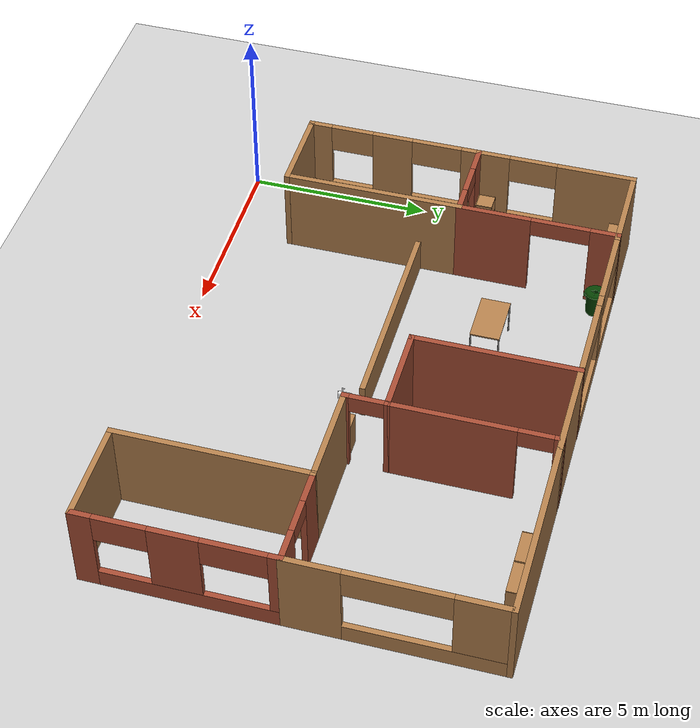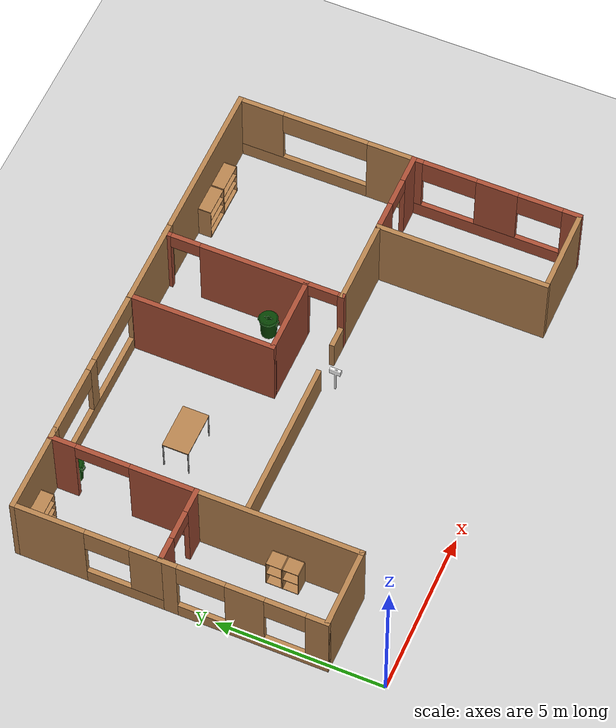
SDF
<sdf version='1.4'>
  <world name='default'>
    <!-- A global light source -->
    <include>
      <uri>model://sun</uri>
    </include>

    <!-- A ground plane -->
    <include>
      <uri>model://ground_plane</uri>
    </include>

    <physics type="ode">
      <max_step_size>0.001</max_step_size>
      <real_time_factor>1</real_time_factor>
      <real_time_update_rate>1000</real_time_update_rate>
      <ode>
        <solver>
          <type>quick</type>
          <iters>100</iters>
          <precon_iters>0</precon_iters>
          <sor>1.400000</sor>
          <use_dynamic_moi_rescaling>1</use_dynamic_moi_rescaling>
        </solver>
        <constraints>
          <cfm>0.00001</cfm>
          <erp>0.2</erp>
          <contact_max_correcting_vel>2000.000000</contact_max_correcting_vel>
          <contact_surface_layer>0.01000</contact_surface_layer>
        </constraints>
      </ode>
    </physics>

    <!-- A turtlebot house -->
    <include>
      <uri>model://turtlebot3_house</uri>
      <pose>7.4 5.6 0 0 0 0</pose>
    </include>

    <gui fullscreen='0'>
      <camera name='user_camera'>
        <pose>9.0 0.0 2.5 0.0 0.5 1.5708</pose>
        <view_controller>orbit</view_controller>
      </camera>
    </gui>
  </world>
</sdf>

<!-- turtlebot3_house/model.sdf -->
<sdf version='1.6'>
  <model name='turtlebot3_house'>
    <link name='Wall_101'>
      <pose frame=''>-0.05 3.1 0 0 0 -1.5708</pose>
      <self_collide>0</self_collide>
      <kinematic>0</kinematic>
      <visual name='Wall_101_Visual'>
        <pose frame=''>0 0 1.25 0 -0 0</pose>
        <geometry>
          <box>
            <size>4.5 0.15 2.5</size>
          </box>
        </geometry>
        <material>
          <script>
            <uri>file://media/materials/scripts/gazebo.material</uri>
            <name>Gazebo/Bricks</name>
          </script>
          <ambient>1 1 1 1</ambient>
          <diffuse>1 1 1 1</diffuse>
          <specular>0.2 0.2 0.2 1</specular>
          <emissive>0 0 0 1</emissive>
        </material>
        <cast_shadows>1</cast_shadows>
        <transparency>0</transparency>
      </visual>
      <collision name='Wall_101_Collision'>
        <laser_retro>0</laser_retro>
        <max_contacts>10</max_contacts>
        <pose frame=''>0 0 1.25 0 -0 0</pose>
        <geometry>
          <box>
            <size>4.5 0.15 2.5</size>
          </box>
        </geometry>
        <surface>
          <friction>
            <ode>
              <mu>1</mu>
              <mu2>1</mu2>
              <fdir1>0 0 0</fdir1>
              <slip1>0</slip1>
              <slip2>0</slip2>
            </ode>
            <torsional>
              <coefficient>1</coefficient>
              <patch_radius>0</patch_radius>
              <surface_radius>0</surface_radius>
              <use_patch_radius>1</use_patch_radius>
              <ode>
                <slip>0</slip>
              </ode>
            </torsional>
          </friction>
          <bounce>
            <restitution_coefficient>0</restitution_coefficient>
            <threshold>1e+06</threshold>
          </bounce>
          <contact>
            <collide_without_contact>0</collide_without_contact>
            <collide_without_contact_bitmask>1</collide_without_contact_bitmask>
            <collide_bitmask>1</collide_bitmask>
            <ode>
              <soft_cfm>0</soft_cfm>
              <soft_erp>0.2</soft_erp>
              <kp>1e+13</kp>
              <kd>1</kd>
              <max_vel>0.01</max_vel>
              <min_depth>0</min_depth>
            </ode>
            <bullet>
              <split_impulse>1</split_impulse>
              <split_impulse_penetration_threshold>-0.01</split_impulse_penetration_threshold>
              <soft_cfm>0</soft_cfm>
              <soft_erp>0.2</soft_erp>
              <kp>1e+13</kp>
              <kd>1</kd>
            </bullet>
          </contact>
        </surface>
      </collision>
    </link>
    <link name='Wall_104'>
      <pose frame=''>2.3 3.1 0 0 -0 1.5708</pose>
      <self_collide>0</self_collide>
      <kinematic>0</kinematic>
      <visual name='Wall_104_Visual_1'>
        <pose frame=''>2.11625 0 1.25 0 -0 0</pose>
        <geometry>
          <box>
            <size>0.267504 0.15 2.5</size>
          </box>
        </geometry>
        <material>
          <script>
            <uri>file://media/materials/scripts/gazebo.material</uri>
            <name>Gazebo/Bricks</name>
          </script>
          <ambient>1 1 1 1</ambient>
          <diffuse>1 1 1 1</diffuse>
          <specular>0.2 0.2 0.2 1</specular>
          <emissive>0 0 0 1</emissive>
        </material>
        <cast_shadows>1</cast_shadows>
        <transparency>0</transparency>
      </visual>
      <visual name='Wall_104_Visual_2'>
        <pose frame=''>1.5325 0 2.25 0 -0 0</pose>
        <geometry>
          <box>
            <size>0.9 0.15 0.5</size>
          </box>
        </geometry>
        <material>
          <script>
            <uri>file://media/materials/scripts/gazebo.material</uri>
            <name>Gazebo/Bricks</name>
          </script>
          <ambient>1 1 1 1</ambient>
          <diffuse>1 1 1 1</diffuse>
          <specular>0.2 0.2 0.2 1</specular>
          <emissive>0 0 0 1</emissive>
        </material>
        <cast_shadows>1</cast_shadows>
        <transparency>0</transparency>
      </visual>
      <visual name='Wall_104_Visual_0'>
        <pose frame=''>-0.583752 0 1.25 0 -0 0</pose>
        <geometry>
          <box>
            <size>3.3325 0.15 2.5</size>
          </box>
        </geometry>
        <material>
          <script>
            <uri>file://media/materials/scripts/gazebo.material</uri>
            <name>Gazebo/Bricks</name>
          </script>
          <ambient>1 1 1 1</ambient>
          <diffuse>1 1 1 1</diffuse>
          <specular>0.2 0.2 0.2 1</specular>
          <emissive>0 0 0 1</emissive>
        </material>
        <cast_shadows>1</cast_shadows>
        <transparency>0</transparency>
      </visual>
      <collision name='Wall_104_Collision_1'>
        <laser_retro>0</laser_retro>
        <max_contacts>10</max_contacts>
        <pose frame=''>2.11625 0 1.25 0 -0 0</pose>
        <geometry>
          <box>
            <size>0.267504 0.15 2.5</size>
          </box>
        </geometry>
        <surface>
          <friction>
            <ode>
              <mu>1</mu>
              <mu2>1</mu2>
              <fdir1>0 0 0</fdir1>
              <slip1>0</slip1>
              <slip2>0</slip2>
            </ode>
            <torsional>
              <coefficient>1</coefficient>
              <patch_radius>0</patch_radius>
              <surface_radius>0</surface_radius>
              <use_patch_radius>1</use_patch_radius>
              <ode>
                <slip>0</slip>
              </ode>
            </torsional>
          </friction>
          <bounce>
            <restitution_coefficient>0</restitution_coefficient>
            <threshold>1e+06</threshold>
          </bounce>
          <contact>
            <collide_without_contact>0</collide_without_contact>
            <collide_without_contact_bitmask>1</collide_without_contact_bitmask>
            <collide_bitmask>1</collide_bitmask>
            <ode>
              <soft_cfm>0</soft_cfm>
              <soft_erp>0.2</soft_erp>
              <kp>1e+13</kp>
              <kd>1</kd>
              <max_vel>0.01</max_vel>
              <min_depth>0</min_depth>
            </ode>
            <bullet>
              <split_impulse>1</split_impulse>
              <split_impulse_penetration_threshold>-0.01</split_impulse_penetration_threshold>
              <soft_cfm>0</soft_cfm>
              <soft_erp>0.2</soft_erp>
              <kp>1e+13</kp>
              <kd>1</kd>
            </bullet>
          </contact>
        </surface>
      </collision>
      <collision name='Wall_104_Collision_2'>
        <laser_retro>0</laser_retro>
        <max_contacts>10</max_contacts>
        <pose frame=''>1.5325 0 2.25 0 -0 0</pose>
        <geometry>
          <box>
            <size>0.9 0.15 0.5</size>
          </box>
        </geometry>
        <surface>
          <friction>
            <ode>
              <mu>1</mu>
              <mu2>1</mu2>
              <fdir1>0 0 0</fdir1>
              <slip1>0</slip1>
              <slip2>0</slip2>
            </ode>
            <torsional>
              <coefficient>1</coefficient>
              <patch_radius>0</patch_radius>
              <surface_radius>0</surface_radius>
              <use_patch_radius>1</use_patch_radius>
              <ode>
                <slip>0</slip>
              </ode>
            </torsional>
          </friction>
          <bounce>
            <restitution_coefficient>0</restitution_coefficient>
            <threshold>1e+06</threshold>
          </bounce>
          <contact>
            <collide_without_contact>0</collide_without_contact>
            <collide_without_contact_bitmask>1</collide_without_contact_bitmask>
            <collide_bitmask>1</collide_bitmask>
            <ode>
              <soft_cfm>0</soft_cfm>
              <soft_erp>0.2</soft_erp>
              <kp>1e+13</kp>
              <kd>1</kd>
              <max_vel>0.01</max_vel>
              <min_depth>0</min_depth>
            </ode>
            <bullet>
              <split_impulse>1</split_impulse>
              <split_impulse_penetration_threshold>-0.01</split_impulse_penetration_threshold>
              <soft_cfm>0</soft_cfm>
              <soft_erp>0.2</soft_erp>
              <kp>1e+13</kp>
              <kd>1</kd>
            </bullet>
          </contact>
        </surface>
      </collision>
      <collision name='Wall_104_Collision_0'>
        <laser_retro>0</laser_retro>
        <max_contacts>10</max_contacts>
        <pose frame=''>-0.583752 0 1.25 0 -0 0</pose>
        <geometry>
          <box>
            <size>3.3325 0.15 2.5</size>
          </box>
        </geometry>
        <surface>
          <friction>
            <ode>
              <mu>1</mu>
              <mu2>1</mu2>
              <fdir1>0 0 0</fdir1>
              <slip1>0</slip1>
              <slip2>0</slip2>
            </ode>
            <torsional>
              <coefficient>1</coefficient>
              <patch_radius>0</patch_radius>
              <surface_radius>0</surface_radius>
              <use_patch_radius>1</use_patch_radius>
              <ode>
                <slip>0</slip>
              </ode>
            </torsional>
          </friction>
          <bounce>
            <restitution_coefficient>0</restitution_coefficient>
            <threshold>1e+06</threshold>
          </bounce>
          <contact>
            <collide_without_contact>0</collide_without_contact>
            <collide_without_contact_bitmask>1</collide_without_contact_bitmask>
            <collide_bitmask>1</collide_bitmask>
            <ode>
              <soft_cfm>0</soft_cfm>
              <soft_erp>0.2</soft_erp>
              <kp>1e+13</kp>
              <kd>1</kd>
              <max_vel>0.01</max_vel>
              <min_depth>0</min_depth>
            </ode>
            <bullet>
              <split_impulse>1</split_impulse>
              <split_impulse_penetration_threshold>-0.01</split_impulse_penetration_threshold>
              <soft_cfm>0</soft_cfm>
              <soft_erp>0.2</soft_erp>
              <kp>1e+13</kp>
              <kd>1</kd>
            </bullet>
          </contact>
        </surface>
      </collision>
    </link>
    <link name='Wall_106'>
      <pose frame=''>6.2 -0.175 0 0 -0 0</pose>
      <self_collide>0</self_collide>
      <kinematic>0</kinematic>
      <visual name='Wall_106_Visual_1'>
        <pose frame=''>0.922235 0 1.25 0 -0 0</pose>
        <geometry>
          <box>
            <size>0.905529 0.15 2.5</size>
          </box>
        </geometry>
        <material>
          <script>
            <uri>file://media/materials/scripts/gazebo.material</uri>
            <name>Gazebo/Bricks</name>
          </script>
          <ambient>1 1 1 1</ambient>
          <diffuse>1 1 1 1</diffuse>
          <specular>0.2 0.2 0.2 1</specular>
          <emissive>0 0 0 1</emissive>
        </material>
        <cast_shadows>1</cast_shadows>
        <transparency>0</transparency>
      </visual>
      <visual name='Wall_106_Visual_2'>
        <pose frame=''>0.019471 0 2.25 0 -0 0</pose>
        <geometry>
          <box>
            <size>0.9 0.15 0.5</size>
          </box>
        </geometry>
        <material>
          <script>
            <uri>file://media/materials/scripts/gazebo.material</uri>
            <name>Gazebo/Bricks</name>
          </script>
          <ambient>1 1 1 1</ambient>
          <diffuse>1 1 1 1</diffuse>
          <specular>0.2 0.2 0.2 1</specular>
          <emissive>0 0 0 1</emissive>
        </material>
        <cast_shadows>1</cast_shadows>
        <transparency>0</transparency>
      </visual>
      <visual name='Wall_106_Visual_0'>
        <pose frame=''>-0.902765 0 1.25 0 -0 0</pose>
        <geometry>
          <box>
            <size>0.944471 0.15 2.5</size>
          </box>
        </geometry>
        <material>
          <script>
            <uri>file://media/materials/scripts/gazebo.material</uri>
            <name>Gazebo/Bricks</name>
          </script>
          <ambient>1 1 1 1</ambient>
          <diffuse>1 1 1 1</diffuse>
          <specular>0.2 0.2 0.2 1</specular>
          <emissive>0 0 0 1</emissive>
        </material>
        <cast_shadows>1</cast_shadows>
        <transparency>0</transparency>
      </visual>
      <collision name='Wall_106_Collision_1'>
        <laser_retro>0</laser_retro>
        <max_contacts>10</max_contacts>
        <pose frame=''>0.922235 0 1.25 0 -0 0</pose>
        <geometry>
          <box>
            <size>0.905529 0.15 2.5</size>
          </box>
        </geometry>
        <surface>
          <friction>
            <ode>
              <mu>1</mu>
              <mu2>1</mu2>
              <fdir1>0 0 0</fdir1>
              <slip1>0</slip1>
              <slip2>0</slip2>
            </ode>
            <torsional>
              <coefficient>1</coefficient>
              <patch_radius>0</patch_radius>
              <surface_radius>0</surface_radius>
              <use_patch_radius>1</use_patch_radius>
              <ode>
                <slip>0</slip>
              </ode>
            </torsional>
          </friction>
          <bounce>
            <restitution_coefficient>0</restitution_coefficient>
            <threshold>1e+06</threshold>
          </bounce>
          <contact>
            <collide_without_contact>0</collide_without_contact>
            <collide_without_contact_bitmask>1</collide_without_contact_bitmask>
            <collide_bitmask>1</collide_bitmask>
            <ode>
              <soft_cfm>0</soft_cfm>
              <soft_erp>0.2</soft_erp>
              <kp>1e+13</kp>
              <kd>1</kd>
              <max_vel>0.01</max_vel>
              <min_depth>0</min_depth>
            </ode>
            <bullet>
              <split_impulse>1</split_impulse>
              <split_impulse_penetration_threshold>-0.01</split_impulse_penetration_threshold>
              <soft_cfm>0</soft_cfm>
              <soft_erp>0.2</soft_erp>
              <kp>1e+13</kp>
              <kd>1</kd>
            </bullet>
          </contact>
        </surface>
      </collision>
      <collision name='Wall_106_Collision_0'>
        <laser_retro>0</laser_retro>
        <max_contacts>10</max_contacts>
        <pose frame=''>-0.902765 0 1.25 0 -0 0</pose>
        <geometry>
          <box>
            <size>0.944471 0.15 2.5</size>
          </box>
        </geometry>
        <surface>
          <friction>
            <ode>
              <mu>1</mu>
              <mu2>1</mu2>
              <fdir1>0 0 0</fdir1>
              <slip1>0</slip1>
              <slip2>0</slip2>
            </ode>
            <torsional>
              <coefficient>1</coefficient>
              <patch_radius>0</patch_radius>
              <surface_radius>0</surface_radius>
              <use_patch_radius>1</use_patch_radius>
              <ode>
                <slip>0</slip>
              </ode>
            </torsional>
          </friction>
          <bounce>
            <restitution_coefficient>0</restitution_coefficient>
            <threshold>1e+06</threshold>
          </bounce>
          <contact>
            <collide_without_contact>0</collide_without_contact>
            <collide_without_contact_bitmask>1</collide_without_contact_bitmask>
            <collide_bitmask>1</collide_bitmask>
            <ode>
              <soft_cfm>0</soft_cfm>
              <soft_erp>0.2</soft_erp>
              <kp>1e+13</kp>
              <kd>1</kd>
              <max_vel>0.01</max_vel>
              <min_depth>0</min_depth>
            </ode>
            <bullet>
              <split_impulse>1</split_impulse>
              <split_impulse_penetration_threshold>-0.01</split_impulse_penetration_threshold>
              <soft_cfm>0</soft_cfm>
              <soft_erp>0.2</soft_erp>
              <kp>1e+13</kp>
              <kd>1</kd>
            </bullet>
          </contact>
        </surface>
      </collision>
      <collision name='Wall_106_Collision_2'>
        <laser_retro>0</laser_retro>
        <max_contacts>10</max_contacts>
        <pose frame=''>0.019471 0 2.25 0 -0 0</pose>
        <geometry>
          <box>
            <size>0.9 0.15 0.5</size>
          </box>
        </geometry>
        <surface>
          <friction>
            <ode>
              <mu>1</mu>
              <mu2>1</mu2>
              <fdir1>0 0 0</fdir1>
              <slip1>0</slip1>
              <slip2>0</slip2>
            </ode>
            <torsional>
              <coefficient>1</coefficient>
              <patch_radius>0</patch_radius>
              <surface_radius>0</surface_radius>
              <use_patch_radius>1</use_patch_radius>
              <ode>
                <slip>0</slip>
              </ode>
            </torsional>
          </friction>
          <bounce>
            <restitution_coefficient>0</restitution_coefficient>
            <threshold>1e+06</threshold>
          </bounce>
          <contact>
            <collide_without_contact>0</collide_without_contact>
            <collide_without_contact_bitmask>1</collide_without_contact_bitmask>
            <collide_bitmask>1</collide_bitmask>
            <ode>
              <soft_cfm>0</soft_cfm>
              <soft_erp>0.2</soft_erp>
              <kp>1e+13</kp>
              <kd>1</kd>
              <max_vel>0.01</max_vel>
              <min_depth>0</min_depth>
            </ode>
            <bullet>
              <split_impulse>1</split_impulse>
              <split_impulse_penetration_threshold>-0.01</split_impulse_penetration_threshold>
              <soft_cfm>0</soft_cfm>
              <soft_erp>0.2</soft_erp>
              <kp>1e+13</kp>
              <kd>1</kd>
            </bullet>
          </contact>
        </surface>
      </collision>
    </link>
    <link name='Wall_108'>
      <pose frame=''>-1.37512 -0.17488 0 0 -0 0</pose>
      <self_collide>0</self_collide>
      <kinematic>0</kinematic>
      <visual name='Wall_108_Visual_0'>
        <pose frame=''>-0.856324 0 0.5 0 -0 0</pose>
        <geometry>
          <box>
            <size>5.78735 0.15 1</size>
          </box>
        </geometry>
        <material>
          <script>
            <uri>file://media/materials/scripts/gazebo.material</uri>
            <name>Gazebo/Wood</name>
          </script>
          <ambient>1 1 1 1</ambient>
          <diffuse>1 1 1 1</diffuse>
          <specular>0.2 0.2 0.2 1</specular>
          <emissive>0 0 0 1</emissive>
        </material>
        <cast_shadows>1</cast_shadows>
        <transparency>0</transparency>
      </visual>
      <visual name='Wall_108_Visual_1'>
        <pose frame=''>3.34368 0 0.5 0 -0 0</pose>
        <geometry>
          <box>
            <size>0.812647 0.15 1</size>
          </box>
        </geometry>
        <material>
          <script>
            <uri>file://media/materials/scripts/gazebo.material</uri>
            <name>Gazebo/Wood</name>
          </script>
          <ambient>1 1 1 1</ambient>
          <diffuse>1 1 1 1</diffuse>
          <specular>0.2 0.2 0.2 1</specular>
          <emissive>0 0 0 1</emissive>
        </material>
        <cast_shadows>1</cast_shadows>
        <transparency>0</transparency>
      </visual>
      <collision name='Wall_108_Collision_1'>
        <laser_retro>0</laser_retro>
        <max_contacts>10</max_contacts>
        <pose frame=''>3.34368 0 0.5 0 -0 0</pose>
        <geometry>
          <box>
            <size>0.812647 0.15 1</size>
          </box>
        </geometry>
        <surface>
          <friction>
            <ode>
              <mu>1</mu>
              <mu2>1</mu2>
              <fdir1>0 0 0</fdir1>
              <slip1>0</slip1>
              <slip2>0</slip2>
            </ode>
            <torsional>
              <coefficient>1</coefficient>
              <patch_radius>0</patch_radius>
              <surface_radius>0</surface_radius>
              <use_patch_radius>1</use_patch_radius>
              <ode>
                <slip>0</slip>
              </ode>
            </torsional>
          </friction>
          <bounce>
            <restitution_coefficient>0</restitution_coefficient>
            <threshold>1e+06</threshold>
          </bounce>
          <contact>
            <collide_without_contact>0</collide_without_contact>
            <collide_without_contact_bitmask>1</collide_without_contact_bitmask>
            <collide_bitmask>1</collide_bitmask>
            <ode>
              <soft_cfm>0</soft_cfm>
              <soft_erp>0.2</soft_erp>
              <kp>1e+13</kp>
              <kd>1</kd>
              <max_vel>0.01</max_vel>
              <min_depth>0</min_depth>
            </ode>
            <bullet>
              <split_impulse>1</split_impulse>
              <split_impulse_penetration_threshold>-0.01</split_impulse_penetration_threshold>
              <soft_cfm>0</soft_cfm>
              <soft_erp>0.2</soft_erp>
              <kp>1e+13</kp>
              <kd>1</kd>
            </bullet>
          </contact>
        </surface>
      </collision>
      <collision name='Wall_108_Collision_0'>
        <laser_retro>0</laser_retro>
        <max_contacts>10</max_contacts>
        <pose frame=''>-0.856324 0 0.5 0 -0 0</pose>
        <geometry>
          <box>
            <size>5.78735 0.15 1</size>
          </box>
        </geometry>
        <surface>
          <friction>
            <ode>
              <mu>1</mu>
              <mu2>1</mu2>
              <fdir1>0 0 0</fdir1>
              <slip1>0</slip1>
              <slip2>0</slip2>
            </ode>
            <torsional>
              <coefficient>1</coefficient>
              <patch_radius>0</patch_radius>
              <surface_radius>0</surface_radius>
              <use_patch_radius>1</use_patch_radius>
              <ode>
                <slip>0</slip>
              </ode>
            </torsional>
          </friction>
          <bounce>
            <restitution_coefficient>0</restitution_coefficient>
            <threshold>1e+06</threshold>
          </bounce>
          <contact>
            <collide_without_contact>0</collide_without_contact>
            <collide_without_contact_bitmask>1</collide_without_contact_bitmask>
            <collide_bitmask>1</collide_bitmask>
            <ode>
              <soft_cfm>0</soft_cfm>
              <soft_erp>0.2</soft_erp>
              <kp>1e+13</kp>
              <kd>1</kd>
              <max_vel>0.01</max_vel>
              <min_depth>0</min_depth>
            </ode>
            <bullet>
              <split_impulse>1</split_impulse>
              <split_impulse_penetration_threshold>-0.01</split_impulse_penetration_threshold>
              <soft_cfm>0</soft_cfm>
              <soft_erp>0.2</soft_erp>
              <kp>1e+13</kp>
              <kd>1</kd>
            </bullet>
          </contact>
        </surface>
      </collision>
    </link>
    <link name='Wall_81'>
      <pose frame=''>5.07752 5.2688 0 0 -0 3.14159</pose>
      <self_collide>0</self_collide>
      <kinematic>0</kinematic>
      <visual name='Wall_81_Visual'>
        <pose frame=''>0 0 1.25 0 -0 0</pose>
        <geometry>
          <box>
            <size>5 0.15 2.5</size>
          </box>
        </geometry>
        <material>
          <script>
            <uri>file://media/materials/scripts/gazebo.material</uri>
            <name>Gazebo/Wood</name>
          </script>
          <ambient>1 1 1 1</ambient>
          <diffuse>1 1 1 1</diffuse>
          <specular>0.2 0.2 0.2 1</specular>
          <emissive>0 0 0 1</emissive>
        </material>
        <cast_shadows>1</cast_shadows>
        <transparency>0</transparency>
      </visual>
      <collision name='Wall_81_Collision'>
        <laser_retro>0</laser_retro>
        <max_contacts>10</max_contacts>
        <pose frame=''>0 0 1.25 0 -0 0</pose>
        <geometry>
          <box>
            <size>5 0.15 2.5</size>
          </box>
        </geometry>
        <surface>
          <friction>
            <ode>
              <mu>1</mu>
              <mu2>1</mu2>
              <fdir1>0 0 0</fdir1>
              <slip1>0</slip1>
              <slip2>0</slip2>
            </ode>
            <torsional>
              <coefficient>1</coefficient>
              <patch_radius>0</patch_radius>
              <surface_radius>0</surface_radius>
              <use_patch_radius>1</use_patch_radius>
              <ode>
                <slip>0</slip>
              </ode>
            </torsional>
          </friction>
          <bounce>
            <restitution_coefficient>0</restitution_coefficient>
            <threshold>1e+06</threshold>
          </bounce>
          <contact>
            <collide_without_contact>0</collide_without_contact>
            <collide_without_contact_bitmask>1</collide_without_contact_bitmask>
            <collide_bitmask>1</collide_bitmask>
            <ode>
              <soft_cfm>0</soft_cfm>
              <soft_erp>0.2</soft_erp>
              <kp>1e+13</kp>
              <kd>1</kd>
              <max_vel>0.01</max_vel>
              <min_depth>0</min_depth>
            </ode>
            <bullet>
              <split_impulse>1</split_impulse>
              <split_impulse_penetration_threshold>-0.01</split_impulse_penetration_threshold>
              <soft_cfm>0</soft_cfm>
              <soft_erp>0.2</soft_erp>
              <kp>1e+13</kp>
              <kd>1</kd>
            </bullet>
          </contact>
        </surface>
      </collision>
    </link>
    <link name='Wall_82'>
      <pose frame=''>1.25 5.26876 0 0 -0 3.14159</pose>
      <self_collide>0</self_collide>
      <kinematic>0</kinematic>
      <visual name='Wall_82_Visual'>
        <pose frame=''>0 0 1.25 0 -0 0</pose>
        <geometry>
          <box>
            <size>2.75 0.15 2.5</size>
          </box>
        </geometry>
        <material>
          <script>
            <uri>file://media/materials/scripts/gazebo.material</uri>
            <name>Gazebo/Wood</name>
          </script>
          <ambient>1 1 1 1</ambient>
          <diffuse>1 1 1 1</diffuse>
          <specular>0.2 0.2 0.2 1</specular>
          <emissive>0 0 0 1</emissive>
        </material>
        <cast_shadows>1</cast_shadows>
        <transparency>0</transparency>
      </visual>
      <collision name='Wall_82_Collision'>
        <laser_retro>0</laser_retro>
        <max_contacts>10</max_contacts>
        <pose frame=''>0 0 1.25 0 -0 0</pose>
        <geometry>
          <box>
            <size>2.75 0.15 2.5</size>
          </box>
        </geometry>
        <surface>
          <friction>
            <ode>
              <mu>1</mu>
              <mu2>1</mu2>
              <fdir1>0 0 0</fdir1>
              <slip1>0</slip1>
              <slip2>0</slip2>
            </ode>
            <torsional>
              <coefficient>1</coefficient>
              <patch_radius>0</patch_radius>
              <surface_radius>0</surface_radius>
              <use_patch_radius>1</use_patch_radius>
              <ode>
                <slip>0</slip>
              </ode>
            </torsional>
          </friction>
          <bounce>
            <restitution_coefficient>0</restitution_coefficient>
            <threshold>1e+06</threshold>
          </bounce>
          <contact>
            <collide_without_contact>0</collide_without_contact>
            <collide_without_contact_bitmask>1</collide_without_contact_bitmask>
            <collide_bitmask>1</collide_bitmask>
            <ode>
              <soft_cfm>0</soft_cfm>
              <soft_erp>0.2</soft_erp>
              <kp>1e+13</kp>
              <kd>1</kd>
              <max_vel>0.01</max_vel>
              <min_depth>0</min_depth>
            </ode>
            <bullet>
              <split_impulse>1</split_impulse>
              <split_impulse_penetration_threshold>-0.01</split_impulse_penetration_threshold>
              <soft_cfm>0</soft_cfm>
              <soft_erp>0.2</soft_erp>
              <kp>1e+13</kp>
              <kd>1</kd>
            </bullet>
          </contact>
        </surface>
      </collision>
    </link>
    <link name='Wall_83'>
      <pose frame=''>-2.475 5.275 0 0 -0 3.14159</pose>
      <self_collide>0</self_collide>
      <kinematic>0</kinematic>
      <visual name='Wall_83_Visual_2'>
        <pose frame=''>0.110246 0 1.5 0 -0 0</pose>
        <geometry>
          <box>
            <size>0.37052 0.15 2</size>
          </box>
        </geometry>
        <material>
          <script>
            <uri>file://media/materials/scripts/gazebo.material</uri>
            <name>Gazebo/Wood</name>
          </script>
          <ambient>1 1 1 1</ambient>
          <diffuse>1 1 1 1</diffuse>
          <specular>0.2 0.2 0.2 1</specular>
          <emissive>0 0 0 1</emissive>
        </material>
        <cast_shadows>1</cast_shadows>
        <transparency>0</transparency>
      </visual>
      <visual name='Wall_83_Visual_6'>
        <pose frame=''>1.39775 0 2.1 0 -0 0</pose>
        <geometry>
          <box>
            <size>2.20449 0.15 0.8</size>
          </box>
        </geometry>
        <material>
          <script>
            <uri>file://media/materials/scripts/gazebo.material</uri>
            <name>Gazebo/Wood</name>
          </script>
          <ambient>1 1 1 1</ambient>
          <diffuse>1 1 1 1</diffuse>
          <specular>0.2 0.2 0.2 1</specular>
          <emissive>0 0 0 1</emissive>
        </material>
        <cast_shadows>1</cast_shadows>
        <transparency>0</transparency>
      </visual>
      <visual name='Wall_83_Visual_3'>
        <pose frame=''>0.110246 0 1.5 0 -0 0</pose>
        <geometry>
          <box>
            <size>0.37052 0.15 2</size>
          </box>
        </geometry>
        <material>
          <script>
            <uri>file://media/materials/scripts/gazebo.material</uri>
            <name>Gazebo/Wood</name>
          </script>
          <ambient>1 1 1 1</ambient>
          <diffuse>1 1 1 1</diffuse>
          <specular>0.2 0.2 0.2 1</specular>
          <emissive>0 0 0 1</emissive>
        </material>
        <cast_shadows>1</cast_shadows>
        <transparency>0</transparency>
      </visual>
      <visual name='Wall_83_Visual_1'>
        <pose frame=''>0.080993 0 0.25 0 -0 0</pose>
        <geometry>
          <box>
            <size>4.83801 0.15 0.5</size>
          </box>
        </geometry>
        <material>
          <script>
            <uri>file://media/materials/scripts/gazebo.material</uri>
            <name>Gazebo/Wood</name>
          </script>
          <ambient>1 1 1 1</ambient>
          <diffuse>1 1 1 1</diffuse>
          <specular>0.2 0.2 0.2 1</specular>
          <emissive>0 0 0 1</emissive>
        </material>
        <cast_shadows>1</cast_shadows>
        <transparency>0</transparency>
      </visual>
      <visual name='Wall_83_Visual_4'>
        <pose frame=''>-1.20651 0 2.1 0 -0 0</pose>
        <geometry>
          <box>
            <size>2.263 0.15 0.8</size>
          </box>
        </geometry>
        <material>
          <script>
            <uri>file://media/materials/scripts/gazebo.material</uri>
            <name>Gazebo/Wood</name>
          </script>
          <ambient>1 1 1 1</ambient>
          <diffuse>1 1 1 1</diffuse>
          <specular>0.2 0.2 0.2 1</specular>
          <emissive>0 0 0 1</emissive>
        </material>
        <cast_shadows>1</cast_shadows>
        <transparency>0</transparency>
      </visual>
      <visual name='Wall_83_Visual_5'>
        <pose frame=''>1.39775 0 2.1 0 -0 0</pose>
        <geometry>
          <box>
            <size>2.20449 0.15 0.8</size>
          </box>
        </geometry>
        <material>
          <script>
            <uri>file://media/materials/scripts/gazebo.material</uri>
            <name>Gazebo/Wood</name>
          </script>
          <ambient>1 1 1 1</ambient>
          <diffuse>1 1 1 1</diffuse>
          <specular>0.2 0.2 0.2 1</specular>
          <emissive>0 0 0 1</emissive>
        </material>
        <cast_shadows>1</cast_shadows>
        <transparency>0</transparency>
      </visual>
      <visual name='Wall_83_Visual_0'>
        <pose frame=''>-2.41901 0 1.25 0 -0 0</pose>
        <geometry>
          <box>
            <size>0.161986 0.15 2.5</size>
          </box>
        </geometry>
        <material>
          <script>
            <uri>file://media/materials/scripts/gazebo.material</uri>
            <name>Gazebo/Wood</name>
          </script>
          <ambient>1 1 1 1</ambient>
          <diffuse>1 1 1 1</diffuse>
          <specular>0.2 0.2 0.2 1</specular>
          <emissive>0 0 0 1</emissive>
        </material>
        <cast_shadows>1</cast_shadows>
        <transparency>0</transparency>
      </visual>
      <collision name='Wall_83_Collision_4'>
        <laser_retro>0</laser_retro>
        <max_contacts>10</max_contacts>
        <pose frame=''>-1.20651 0 2.1 0 -0 0</pose>
        <geometry>
          <box>
            <size>2.263 0.15 0.8</size>
          </box>
        </geometry>
        <surface>
          <friction>
            <ode>
              <mu>1</mu>
              <mu2>1</mu2>
              <fdir1>0 0 0</fdir1>
              <slip1>0</slip1>
              <slip2>0</slip2>
            </ode>
            <torsional>
              <coefficient>1</coefficient>
              <patch_radius>0</patch_radius>
              <surface_radius>0</surface_radius>
              <use_patch_radius>1</use_patch_radius>
              <ode>
                <slip>0</slip>
              </ode>
            </torsional>
          </friction>
          <bounce>
            <restitution_coefficient>0</restitution_coefficient>
            <threshold>1e+06</threshold>
          </bounce>
          <contact>
            <collide_without_contact>0</collide_without_contact>
            <collide_without_contact_bitmask>1</collide_without_contact_bitmask>
            <collide_bitmask>1</collide_bitmask>
            <ode>
              <soft_cfm>0</soft_cfm>
              <soft_erp>0.2</soft_erp>
              <kp>1e+13</kp>
              <kd>1</kd>
              <max_vel>0.01</max_vel>
              <min_depth>0</min_depth>
            </ode>
            <bullet>
              <split_impulse>1</split_impulse>
              <split_impulse_penetration_threshold>-0.01</split_impulse_penetration_threshold>
              <soft_cfm>0</soft_cfm>
              <soft_erp>0.2</soft_erp>
              <kp>1e+13</kp>
              <kd>1</kd>
            </bullet>
          </contact>
        </surface>
      </collision>
      <collision name='Wall_83_Collision_2'>
        <laser_retro>0</laser_retro>
        <max_contacts>10</max_contacts>
        <pose frame=''>0.110246 0 1.5 0 -0 0</pose>
        <geometry>
          <box>
            <size>0.37052 0.15 2</size>
          </box>
        </geometry>
        <surface>
          <friction>
            <ode>
              <mu>1</mu>
              <mu2>1</mu2>
              <fdir1>0 0 0</fdir1>
              <slip1>0</slip1>
              <slip2>0</slip2>
            </ode>
            <torsional>
              <coefficient>1</coefficient>
              <patch_radius>0</patch_radius>
              <surface_radius>0</surface_radius>
              <use_patch_radius>1</use_patch_radius>
              <ode>
                <slip>0</slip>
              </ode>
            </torsional>
          </friction>
          <bounce>
            <restitution_coefficient>0</restitution_coefficient>
            <threshold>1e+06</threshold>
          </bounce>
          <contact>
            <collide_without_contact>0</collide_without_contact>
            <collide_without_contact_bitmask>1</collide_without_contact_bitmask>
            <collide_bitmask>1</collide_bitmask>
            <ode>
              <soft_cfm>0</soft_cfm>
              <soft_erp>0.2</soft_erp>
              <kp>1e+13</kp>
              <kd>1</kd>
              <max_vel>0.01</max_vel>
              <min_depth>0</min_depth>
            </ode>
            <bullet>
              <split_impulse>1</split_impulse>
              <split_impulse_penetration_threshold>-0.01</split_impulse_penetration_threshold>
              <soft_cfm>0</soft_cfm>
              <soft_erp>0.2</soft_erp>
              <kp>1e+13</kp>
              <kd>1</kd>
            </bullet>
          </contact>
        </surface>
      </collision>
      <collision name='Wall_83_Collision_6'>
        <laser_retro>0</laser_retro>
        <max_contacts>10</max_contacts>
        <pose frame=''>1.39775 0 2.1 0 -0 0</pose>
        <geometry>
          <box>
            <size>2.20449 0.15 0.8</size>
          </box>
        </geometry>
        <surface>
          <friction>
            <ode>
              <mu>1</mu>
              <mu2>1</mu2>
              <fdir1>0 0 0</fdir1>
              <slip1>0</slip1>
              <slip2>0</slip2>
            </ode>
            <torsional>
              <coefficient>1</coefficient>
              <patch_radius>0</patch_radius>
              <surface_radius>0</surface_radius>
              <use_patch_radius>1</use_patch_radius>
              <ode>
                <slip>0</slip>
              </ode>
            </torsional>
          </friction>
          <bounce>
            <restitution_coefficient>0</restitution_coefficient>
            <threshold>1e+06</threshold>
          </bounce>
          <contact>
            <collide_without_contact>0</collide_without_contact>
            <collide_without_contact_bitmask>1</collide_without_contact_bitmask>
            <collide_bitmask>1</collide_bitmask>
            <ode>
              <soft_cfm>0</soft_cfm>
              <soft_erp>0.2</soft_erp>
              <kp>1e+13</kp>
              <kd>1</kd>
              <max_vel>0.01</max_vel>
              <min_depth>0</min_depth>
            </ode>
            <bullet>
              <split_impulse>1</split_impulse>
              <split_impulse_penetration_threshold>-0.01</split_impulse_penetration_threshold>
              <soft_cfm>0</soft_cfm>
              <soft_erp>0.2</soft_erp>
              <kp>1e+13</kp>
              <kd>1</kd>
            </bullet>
          </contact>
        </surface>
      </collision>
      <collision name='Wall_83_Collision_0'>
        <laser_retro>0</laser_retro>
        <max_contacts>10</max_contacts>
        <pose frame=''>-2.41901 0 1.25 0 -0 0</pose>
        <geometry>
          <box>
            <size>0.161986 0.15 2.5</size>
          </box>
        </geometry>
        <surface>
          <friction>
            <ode>
              <mu>1</mu>
              <mu2>1</mu2>
              <fdir1>0 0 0</fdir1>
              <slip1>0</slip1>
              <slip2>0</slip2>
            </ode>
            <torsional>
              <coefficient>1</coefficient>
              <patch_radius>0</patch_radius>
              <surface_radius>0</surface_radius>
              <use_patch_radius>1</use_patch_radius>
              <ode>
                <slip>0</slip>
              </ode>
            </torsional>
          </friction>
          <bounce>
            <restitution_coefficient>0</restitution_coefficient>
            <threshold>1e+06</threshold>
          </bounce>
          <contact>
            <collide_without_contact>0</collide_without_contact>
            <collide_without_contact_bitmask>1</collide_without_contact_bitmask>
            <collide_bitmask>1</collide_bitmask>
            <ode>
              <soft_cfm>0</soft_cfm>
              <soft_erp>0.2</soft_erp>
              <kp>1e+13</kp>
              <kd>1</kd>
              <max_vel>0.01</max_vel>
              <min_depth>0</min_depth>
            </ode>
            <bullet>
              <split_impulse>1</split_impulse>
              <split_impulse_penetration_threshold>-0.01</split_impulse_penetration_threshold>
              <soft_cfm>0</soft_cfm>
              <soft_erp>0.2</soft_erp>
              <kp>1e+13</kp>
              <kd>1</kd>
            </bullet>
          </contact>
        </surface>
      </collision>
      <collision name='Wall_83_Collision_1'>
        <laser_retro>0</laser_retro>
        <max_contacts>10</max_contacts>
        <pose frame=''>0.080993 0 0.25 0 -0 0</pose>
        <geometry>
          <box>
            <size>4.83801 0.15 0.5</size>
          </box>
        </geometry>
        <surface>
          <friction>
            <ode>
              <mu>1</mu>
              <mu2>1</mu2>
              <fdir1>0 0 0</fdir1>
              <slip1>0</slip1>
              <slip2>0</slip2>
            </ode>
            <torsional>
              <coefficient>1</coefficient>
              <patch_radius>0</patch_radius>
              <surface_radius>0</surface_radius>
              <use_patch_radius>1</use_patch_radius>
              <ode>
                <slip>0</slip>
              </ode>
            </torsional>
          </friction>
          <bounce>
            <restitution_coefficient>0</restitution_coefficient>
            <threshold>1e+06</threshold>
          </bounce>
          <contact>
            <collide_without_contact>0</collide_without_contact>
            <collide_without_contact_bitmask>1</collide_without_contact_bitmask>
            <collide_bitmask>1</collide_bitmask>
            <ode>
              <soft_cfm>0</soft_cfm>
              <soft_erp>0.2</soft_erp>
              <kp>1e+13</kp>
              <kd>1</kd>
              <max_vel>0.01</max_vel>
              <min_depth>0</min_depth>
            </ode>
            <bullet>
              <split_impulse>1</split_impulse>
              <split_impulse_penetration_threshold>-0.01</split_impulse_penetration_threshold>
              <soft_cfm>0</soft_cfm>
              <soft_erp>0.2</soft_erp>
              <kp>1e+13</kp>
              <kd>1</kd>
            </bullet>
          </contact>
        </surface>
      </collision>
      <collision name='Wall_83_Collision_3'>
        <laser_retro>0</laser_retro>
        <max_contacts>10</max_contacts>
        <pose frame=''>0.110246 0 1.5 0 -0 0</pose>
        <geometry>
          <box>
            <size>0.37052 0.15 2</size>
          </box>
        </geometry>
        <surface>
          <friction>
            <ode>
              <mu>1</mu>
              <mu2>1</mu2>
              <fdir1>0 0 0</fdir1>
              <slip1>0</slip1>
              <slip2>0</slip2>
            </ode>
            <torsional>
              <coefficient>1</coefficient>
              <patch_radius>0</patch_radius>
              <surface_radius>0</surface_radius>
              <use_patch_radius>1</use_patch_radius>
              <ode>
                <slip>0</slip>
              </ode>
            </torsional>
          </friction>
          <bounce>
            <restitution_coefficient>0</restitution_coefficient>
            <threshold>1e+06</threshold>
          </bounce>
          <contact>
            <collide_without_contact>0</collide_without_contact>
            <collide_without_contact_bitmask>1</collide_without_contact_bitmask>
            <collide_bitmask>1</collide_bitmask>
            <ode>
              <soft_cfm>0</soft_cfm>
              <soft_erp>0.2</soft_erp>
              <kp>1e+13</kp>
              <kd>1</kd>
              <max_vel>0.01</max_vel>
              <min_depth>0</min_depth>
            </ode>
            <bullet>
              <split_impulse>1</split_impulse>
              <split_impulse_penetration_threshold>-0.01</split_impulse_penetration_threshold>
              <soft_cfm>0</soft_cfm>
              <soft_erp>0.2</soft_erp>
              <kp>1e+13</kp>
              <kd>1</kd>
            </bullet>
          </contact>
        </surface>
      </collision>
      <collision name='Wall_83_Collision_5'>
        <laser_retro>0</laser_retro>
        <max_contacts>10</max_contacts>
        <pose frame=''>1.39775 0 2.1 0 -0 0</pose>
        <geometry>
          <box>
            <size>2.20449 0.15 0.8</size>
          </box>
        </geometry>
        <surface>
          <friction>
            <ode>
              <mu>1</mu>
              <mu2>1</mu2>
              <fdir1>0 0 0</fdir1>
              <slip1>0</slip1>
              <slip2>0</slip2>
            </ode>
            <torsional>
              <coefficient>1</coefficient>
              <patch_radius>0</patch_radius>
              <surface_radius>0</surface_radius>
              <use_patch_radius>1</use_patch_radius>
              <ode>
                <slip>0</slip>
              </ode>
            </torsional>
          </friction>
          <bounce>
            <restitution_coefficient>0</restitution_coefficient>
            <threshold>1e+06</threshold>
          </bounce>
          <contact>
            <collide_without_contact>0</collide_without_contact>
            <collide_without_contact_bitmask>1</collide_without_contact_bitmask>
            <collide_bitmask>1</collide_bitmask>
            <ode>
              <soft_cfm>0</soft_cfm>
              <soft_erp>0.2</soft_erp>
              <kp>1e+13</kp>
              <kd>1</kd>
              <max_vel>0.01</max_vel>
              <min_depth>0</min_depth>
            </ode>
            <bullet>
              <split_impulse>1</split_impulse>
              <split_impulse_penetration_threshold>-0.01</split_impulse_penetration_threshold>
              <soft_cfm>0</soft_cfm>
              <soft_erp>0.2</soft_erp>
              <kp>1e+13</kp>
              <kd>1</kd>
            </bullet>
          </contact>
        </surface>
      </collision>
    </link>
    <link name='Wall_84'>
      <pose frame=''>-6.2 5.275 0 0 -0 3.14159</pose>
      <self_collide>0</self_collide>
      <kinematic>0</kinematic>
      <visual name='Wall_84_Visual'>
        <pose frame=''>0 0 1.25 0 -0 0</pose>
        <geometry>
          <box>
            <size>2.75 0.15 2.5</size>
          </box>
        </geometry>
        <material>
          <script>
            <uri>file://media/materials/scripts/gazebo.material</uri>
            <name>Gazebo/Wood</name>
          </script>
          <ambient>1 1 1 1</ambient>
          <diffuse>1 1 1 1</diffuse>
          <specular>0.2 0.2 0.2 1</specular>
          <emissive>0 0 0 1</emissive>
        </material>
        <cast_shadows>1</cast_shadows>
        <transparency>0</transparency>
      </visual>
      <collision name='Wall_84_Collision'>
        <laser_retro>0</laser_retro>
        <max_contacts>10</max_contacts>
        <pose frame=''>0 0 1.25 0 -0 0</pose>
        <geometry>
          <box>
            <size>2.75 0.15 2.5</size>
          </box>
        </geometry>
        <surface>
          <friction>
            <ode>
              <mu>1</mu>
              <mu2>1</mu2>
              <fdir1>0 0 0</fdir1>
              <slip1>0</slip1>
              <slip2>0</slip2>
            </ode>
            <torsional>
              <coefficient>1</coefficient>
              <patch_radius>0</patch_radius>
              <surface_radius>0</surface_radius>
              <use_patch_radius>1</use_patch_radius>
              <ode>
                <slip>0</slip>
              </ode>
            </torsional>
          </friction>
          <bounce>
            <restitution_coefficient>0</restitution_coefficient>
            <threshold>1e+06</threshold>
          </bounce>
          <contact>
            <collide_without_contact>0</collide_without_contact>
            <collide_without_contact_bitmask>1</collide_without_contact_bitmask>
            <collide_bitmask>1</collide_bitmask>
            <ode>
              <soft_cfm>0</soft_cfm>
              <soft_erp>0.2</soft_erp>
              <kp>1e+13</kp>
              <kd>1</kd>
              <max_vel>0.01</max_vel>
              <min_depth>0</min_depth>
            </ode>
            <bullet>
              <split_impulse>1</split_impulse>
              <split_impulse_penetration_threshold>-0.01</split_impulse_penetration_threshold>
              <soft_cfm>0</soft_cfm>
              <soft_erp>0.2</soft_erp>
              <kp>1e+13</kp>
              <kd>1</kd>
            </bullet>
          </contact>
        </surface>
      </collision>
    </link>
    <link name='Wall_85'>
      <pose frame=''>-7.5 3.1 0 0 0 -1.5708</pose>
      <self_collide>0</self_collide>
      <kinematic>0</kinematic>
      <visual name='Wall_85_Visual_3'>
        <pose frame=''>0.62212 0 2.1 0 -0 0</pose>
        <geometry>
          <box>
            <size>1.332 0.15 0.8</size>
          </box>
        </geometry>
        <material>
          <script>
            <uri>file://media/materials/scripts/gazebo.material</uri>
            <name>Gazebo/Wood</name>
          </script>
          <ambient>1 1 1 1</ambient>
          <diffuse>1 1 1 1</diffuse>
          <specular>0.2 0.2 0.2 1</specular>
          <emissive>0 0 0 1</emissive>
        </material>
        <cast_shadows>1</cast_shadows>
        <transparency>0</transparency>
      </visual>
      <visual name='Wall_85_Visual_2'>
        <pose frame=''>1.76906 0 1.5 0 -0 0</pose>
        <geometry>
          <box>
            <size>0.96188 0.15 2</size>
          </box>
        </geometry>
        <material>
          <script>
            <uri>file://media/materials/scripts/gazebo.material</uri>
            <name>Gazebo/Wood</name>
          </script>
          <ambient>1 1 1 1</ambient>
          <diffuse>1 1 1 1</diffuse>
          <specular>0.2 0.2 0.2 1</specular>
          <emissive>0 0 0 1</emissive>
        </material>
        <cast_shadows>1</cast_shadows>
        <transparency>0</transparency>
      </visual>
      <visual name='Wall_85_Visual_0'>
        <pose frame=''>-1.14694 0 1.25 0 -0 0</pose>
        <geometry>
          <box>
            <size>2.20612 0.15 2.5</size>
          </box>
        </geometry>
        <material>
          <script>
            <uri>file://media/materials/scripts/gazebo.material</uri>
            <name>Gazebo/Wood</name>
          </script>
          <ambient>1 1 1 1</ambient>
          <diffuse>1 1 1 1</diffuse>
          <specular>0.2 0.2 0.2 1</specular>
          <emissive>0 0 0 1</emissive>
        </material>
        <cast_shadows>1</cast_shadows>
        <transparency>0</transparency>
      </visual>
      <visual name='Wall_85_Visual_1'>
        <pose frame=''>1.10306 0 0.25 0 -0 0</pose>
        <geometry>
          <box>
            <size>2.29388 0.15 0.5</size>
          </box>
        </geometry>
        <material>
          <script>
            <uri>file://media/materials/scripts/gazebo.material</uri>
            <name>Gazebo/Wood</name>
          </script>
          <ambient>1 1 1 1</ambient>
          <diffuse>1 1 1 1</diffuse>
          <specular>0.2 0.2 0.2 1</specular>
          <emissive>0 0 0 1</emissive>
        </material>
        <cast_shadows>1</cast_shadows>
        <transparency>0</transparency>
      </visual>
      <collision name='Wall_85_Collision_3'>
        <laser_retro>0</laser_retro>
        <max_contacts>10</max_contacts>
        <pose frame=''>0.62212 0 2.1 0 -0 0</pose>
        <geometry>
          <box>
            <size>1.332 0.15 0.8</size>
          </box>
        </geometry>
        <surface>
          <friction>
            <ode>
              <mu>1</mu>
              <mu2>1</mu2>
              <fdir1>0 0 0</fdir1>
              <slip1>0</slip1>
              <slip2>0</slip2>
            </ode>
            <torsional>
              <coefficient>1</coefficient>
              <patch_radius>0</patch_radius>
              <surface_radius>0</surface_radius>
              <use_patch_radius>1</use_patch_radius>
              <ode>
                <slip>0</slip>
              </ode>
            </torsional>
          </friction>
          <bounce>
            <restitution_coefficient>0</restitution_coefficient>
            <threshold>1e+06</threshold>
          </bounce>
          <contact>
            <collide_without_contact>0</collide_without_contact>
            <collide_without_contact_bitmask>1</collide_without_contact_bitmask>
            <collide_bitmask>1</collide_bitmask>
            <ode>
              <soft_cfm>0</soft_cfm>
              <soft_erp>0.2</soft_erp>
              <kp>1e+13</kp>
              <kd>1</kd>
              <max_vel>0.01</max_vel>
              <min_depth>0</min_depth>
            </ode>
            <bullet>
              <split_impulse>1</split_impulse>
              <split_impulse_penetration_threshold>-0.01</split_impulse_penetration_threshold>
              <soft_cfm>0</soft_cfm>
              <soft_erp>0.2</soft_erp>
              <kp>1e+13</kp>
              <kd>1</kd>
            </bullet>
          </contact>
        </surface>
      </collision>
      <collision name='Wall_85_Collision_2'>
        <laser_retro>0</laser_retro>
        <max_contacts>10</max_contacts>
        <pose frame=''>1.76906 0 1.5 0 -0 0</pose>
        <geometry>
          <box>
            <size>0.96188 0.15 2</size>
          </box>
        </geometry>
        <surface>
          <friction>
            <ode>
              <mu>1</mu>
              <mu2>1</mu2>
              <fdir1>0 0 0</fdir1>
              <slip1>0</slip1>
              <slip2>0</slip2>
            </ode>
            <torsional>
              <coefficient>1</coefficient>
              <patch_radius>0</patch_radius>
              <surface_radius>0</surface_radius>
              <use_patch_radius>1</use_patch_radius>
              <ode>
                <slip>0</slip>
              </ode>
            </torsional>
          </friction>
          <bounce>
            <restitution_coefficient>0</restitution_coefficient>
            <threshold>1e+06</threshold>
          </bounce>
          <contact>
            <collide_without_contact>0</collide_without_contact>
            <collide_without_contact_bitmask>1</collide_without_contact_bitmask>
            <collide_bitmask>1</collide_bitmask>
            <ode>
              <soft_cfm>0</soft_cfm>
              <soft_erp>0.2</soft_erp>
              <kp>1e+13</kp>
              <kd>1</kd>
              <max_vel>0.01</max_vel>
              <min_depth>0</min_depth>
            </ode>
            <bullet>
              <split_impulse>1</split_impulse>
              <split_impulse_penetration_threshold>-0.01</split_impulse_penetration_threshold>
              <soft_cfm>0</soft_cfm>
              <soft_erp>0.2</soft_erp>
              <kp>1e+13</kp>
              <kd>1</kd>
            </bullet>
          </contact>
        </surface>
      </collision>
      <collision name='Wall_85_Collision_1'>
        <laser_retro>0</laser_retro>
        <max_contacts>10</max_contacts>
        <pose frame=''>1.10306 0 0.25 0 -0 0</pose>
        <geometry>
          <box>
            <size>2.29388 0.15 0.5</size>
          </box>
        </geometry>
        <surface>
          <friction>
            <ode>
              <mu>1</mu>
              <mu2>1</mu2>
              <fdir1>0 0 0</fdir1>
              <slip1>0</slip1>
              <slip2>0</slip2>
            </ode>
            <torsional>
              <coefficient>1</coefficient>
              <patch_radius>0</patch_radius>
              <surface_radius>0</surface_radius>
              <use_patch_radius>1</use_patch_radius>
              <ode>
                <slip>0</slip>
              </ode>
            </torsional>
          </friction>
          <bounce>
            <restitution_coefficient>0</restitution_coefficient>
            <threshold>1e+06</threshold>
          </bounce>
          <contact>
            <collide_without_contact>0</collide_without_contact>
            <collide_without_contact_bitmask>1</collide_without_contact_bitmask>
            <collide_bitmask>1</collide_bitmask>
            <ode>
              <soft_cfm>0</soft_cfm>
              <soft_erp>0.2</soft_erp>
              <kp>1e+13</kp>
              <kd>1</kd>
              <max_vel>0.01</max_vel>
              <min_depth>0</min_depth>
            </ode>
            <bullet>
              <split_impulse>1</split_impulse>
              <split_impulse_penetration_threshold>-0.01</split_impulse_penetration_threshold>
              <soft_cfm>0</soft_cfm>
              <soft_erp>0.2</soft_erp>
              <kp>1e+13</kp>
              <kd>1</kd>
            </bullet>
          </contact>
        </surface>
      </collision>
      <collision name='Wall_85_Collision_0'>
        <laser_retro>0</laser_retro>
        <max_contacts>10</max_contacts>
        <pose frame=''>-1.14694 0 1.25 0 -0 0</pose>
        <geometry>
          <box>
            <size>2.20612 0.15 2.5</size>
          </box>
        </geometry>
        <surface>
          <friction>
            <ode>
              <mu>1</mu>
              <mu2>1</mu2>
              <fdir1>0 0 0</fdir1>
              <slip1>0</slip1>
              <slip2>0</slip2>
            </ode>
            <torsional>
              <coefficient>1</coefficient>
              <patch_radius>0</patch_radius>
              <surface_radius>0</surface_radius>
              <use_patch_radius>1</use_patch_radius>
              <ode>
                <slip>0</slip>
              </ode>
            </torsional>
          </friction>
          <bounce>
            <restitution_coefficient>0</restitution_coefficient>
            <threshold>1e+06</threshold>
          </bounce>
          <contact>
            <collide_without_contact>0</collide_without_contact>
            <collide_without_contact_bitmask>1</collide_without_contact_bitmask>
            <collide_bitmask>1</collide_bitmask>
            <ode>
              <soft_cfm>0</soft_cfm>
              <soft_erp>0.2</soft_erp>
              <kp>1e+13</kp>
              <kd>1</kd>
              <max_vel>0.01</max_vel>
              <min_depth>0</min_depth>
            </ode>
            <bullet>
              <split_impulse>1</split_impulse>
              <split_impulse_penetration_threshold>-0.01</split_impulse_penetration_threshold>
              <soft_cfm>0</soft_cfm>
              <soft_erp>0.2</soft_erp>
              <kp>1e+13</kp>
              <kd>1</kd>
            </bullet>
          </contact>
        </surface>
      </collision>
    </link>
    <link name='Wall_86'>
      <pose frame=''>-7.5 -1.5 0 0 0 -1.5708</pose>
      <self_collide>0</self_collide>
      <kinematic>0</kinematic>
      <visual name='Wall_86_Visual_1'>
        <pose frame=''>0.28462 0 0.25 0 -0 0</pose>
        <geometry>
          <box>
            <size>4.43076 0.15 0.5</size>
          </box>
        </geometry>
        <material>
          <script>
            <uri>file://media/materials/scripts/gazebo.material</uri>
            <name>Gazebo/Wood</name>
          </script>
          <ambient>1 1 1 1</ambient>
          <diffuse>1 1 1 1</diffuse>
          <specular>0.2 0.2 0.2 1</specular>
          <emissive>0 0 0 1</emissive>
        </material>
        <cast_shadows>1</cast_shadows>
        <transparency>0</transparency>
      </visual>
      <visual name='Wall_86_Visual_4'>
        <pose frame=''>-1.22476 0 2.1 0 -0 0</pose>
        <geometry>
          <box>
            <size>1.412 0.15 0.8</size>
          </box>
        </geometry>
        <material>
          <script>
            <uri>file://media/materials/scripts/gazebo.material</uri>
            <name>Gazebo/Wood</name>
          </script>
          <ambient>1 1 1 1</ambient>
          <diffuse>1 1 1 1</diffuse>
          <specular>0.2 0.2 0.2 1</specular>
          <emissive>0 0 0 1</emissive>
        </material>
        <cast_shadows>1</cast_shadows>
        <transparency>0</transparency>
      </visual>
      <visual name='Wall_86_Visual_0'>
        <pose frame=''>-2.21538 0 1.25 0 -0 0</pose>
        <geometry>
          <box>
            <size>0.569241 0.15 2.5</size>
          </box>
        </geometry>
        <material>
          <script>
            <uri>file://media/materials/scripts/gazebo.material</uri>
            <name>Gazebo/Wood</name>
          </script>
          <ambient>1 1 1 1</ambient>
          <diffuse>1 1 1 1</diffuse>
          <specular>0.2 0.2 0.2 1</specular>
          <emissive>0 0 0 1</emissive>
        </material>
        <cast_shadows>1</cast_shadows>
        <transparency>0</transparency>
      </visual>
      <visual name='Wall_86_Visual_5'>
        <pose frame=''>1.22246 0 2.1 0 -0 0</pose>
        <geometry>
          <box>
            <size>1.199 0.15 0.8</size>
          </box>
        </geometry>
        <material>
          <script>
            <uri>file://media/materials/scripts/gazebo.material</uri>
            <name>Gazebo/Wood</name>
          </script>
          <ambient>1 1 1 1</ambient>
          <diffuse>1 1 1 1</diffuse>
          <specular>0.2 0.2 0.2 1</specular>
          <emissive>0 0 0 1</emissive>
        </material>
        <cast_shadows>1</cast_shadows>
        <transparency>0</transparency>
      </visual>
      <visual name='Wall_86_Visual_2'>
        <pose frame=''>0.0521 0 1.5 0 -0 0</pose>
        <geometry>
          <box>
            <size>1.14172 0.15 2</size>
          </box>
        </geometry>
        <material>
          <script>
            <uri>file://media/materials/scripts/gazebo.material</uri>
            <name>Gazebo/Wood</name>
          </script>
          <ambient>1 1 1 1</ambient>
          <diffuse>1 1 1 1</diffuse>
          <specular>0.2 0.2 0.2 1</specular>
          <emissive>0 0 0 1</emissive>
        </material>
        <cast_shadows>1</cast_shadows>
        <transparency>0</transparency>
      </visual>
      <visual name='Wall_86_Visual_3'>
        <pose frame=''>2.16098 0 1.5 0 -0 0</pose>
        <geometry>
          <box>
            <size>0.678041 0.15 2</size>
          </box>
        </geometry>
        <material>
          <script>
            <uri>file://media/materials/scripts/gazebo.material</uri>
            <name>Gazebo/Wood</name>
          </script>
          <ambient>1 1 1 1</ambient>
          <diffuse>1 1 1 1</diffuse>
          <specular>0.2 0.2 0.2 1</specular>
          <emissive>0 0 0 1</emissive>
        </material>
        <cast_shadows>1</cast_shadows>
        <transparency>0</transparency>
      </visual>
      <collision name='Wall_86_Collision_4'>
        <laser_retro>0</laser_retro>
        <max_contacts>10</max_contacts>
        <pose frame=''>-1.22476 0 2.1 0 -0 0</pose>
        <geometry>
          <box>
            <size>1.412 0.15 0.8</size>
          </box>
        </geometry>
        <surface>
          <friction>
            <ode>
              <mu>1</mu>
              <mu2>1</mu2>
              <fdir1>0 0 0</fdir1>
              <slip1>0</slip1>
              <slip2>0</slip2>
            </ode>
            <torsional>
              <coefficient>1</coefficient>
              <patch_radius>0</patch_radius>
              <surface_radius>0</surface_radius>
              <use_patch_radius>1</use_patch_radius>
              <ode>
                <slip>0</slip>
              </ode>
            </torsional>
          </friction>
          <bounce>
            <restitution_coefficient>0</restitution_coefficient>
            <threshold>1e+06</threshold>
          </bounce>
          <contact>
            <collide_without_contact>0</collide_without_contact>
            <collide_without_contact_bitmask>1</collide_without_contact_bitmask>
            <collide_bitmask>1</collide_bitmask>
            <ode>
              <soft_cfm>0</soft_cfm>
              <soft_erp>0.2</soft_erp>
              <kp>1e+13</kp>
              <kd>1</kd>
              <max_vel>0.01</max_vel>
              <min_depth>0</min_depth>
            </ode>
            <bullet>
              <split_impulse>1</split_impulse>
              <split_impulse_penetration_threshold>-0.01</split_impulse_penetration_threshold>
              <soft_cfm>0</soft_cfm>
              <soft_erp>0.2</soft_erp>
              <kp>1e+13</kp>
              <kd>1</kd>
            </bullet>
          </contact>
        </surface>
      </collision>
      <collision name='Wall_86_Collision_5'>
        <laser_retro>0</laser_retro>
        <max_contacts>10</max_contacts>
        <pose frame=''>1.22246 0 2.1 0 -0 0</pose>
        <geometry>
          <box>
            <size>1.199 0.15 0.8</size>
          </box>
        </geometry>
        <surface>
          <friction>
            <ode>
              <mu>1</mu>
              <mu2>1</mu2>
              <fdir1>0 0 0</fdir1>
              <slip1>0</slip1>
              <slip2>0</slip2>
            </ode>
            <torsional>
              <coefficient>1</coefficient>
              <patch_radius>0</patch_radius>
              <surface_radius>0</surface_radius>
              <use_patch_radius>1</use_patch_radius>
              <ode>
                <slip>0</slip>
              </ode>
            </torsional>
          </friction>
          <bounce>
            <restitution_coefficient>0</restitution_coefficient>
            <threshold>1e+06</threshold>
          </bounce>
          <contact>
            <collide_without_contact>0</collide_without_contact>
            <collide_without_contact_bitmask>1</collide_without_contact_bitmask>
            <collide_bitmask>1</collide_bitmask>
            <ode>
              <soft_cfm>0</soft_cfm>
              <soft_erp>0.2</soft_erp>
              <kp>1e+13</kp>
              <kd>1</kd>
              <max_vel>0.01</max_vel>
              <min_depth>0</min_depth>
            </ode>
            <bullet>
              <split_impulse>1</split_impulse>
              <split_impulse_penetration_threshold>-0.01</split_impulse_penetration_threshold>
              <soft_cfm>0</soft_cfm>
              <soft_erp>0.2</soft_erp>
              <kp>1e+13</kp>
              <kd>1</kd>
            </bullet>
          </contact>
        </surface>
      </collision>
      <collision name='Wall_86_Collision_2'>
        <laser_retro>0</laser_retro>
        <max_contacts>10</max_contacts>
        <pose frame=''>0.0521 0 1.5 0 -0 0</pose>
        <geometry>
          <box>
            <size>1.14172 0.15 2</size>
          </box>
        </geometry>
        <surface>
          <friction>
            <ode>
              <mu>1</mu>
              <mu2>1</mu2>
              <fdir1>0 0 0</fdir1>
              <slip1>0</slip1>
              <slip2>0</slip2>
            </ode>
            <torsional>
              <coefficient>1</coefficient>
              <patch_radius>0</patch_radius>
              <surface_radius>0</surface_radius>
              <use_patch_radius>1</use_patch_radius>
              <ode>
                <slip>0</slip>
              </ode>
            </torsional>
          </friction>
          <bounce>
            <restitution_coefficient>0</restitution_coefficient>
            <threshold>1e+06</threshold>
          </bounce>
          <contact>
            <collide_without_contact>0</collide_without_contact>
            <collide_without_contact_bitmask>1</collide_without_contact_bitmask>
            <collide_bitmask>1</collide_bitmask>
            <ode>
              <soft_cfm>0</soft_cfm>
              <soft_erp>0.2</soft_erp>
              <kp>1e+13</kp>
              <kd>1</kd>
              <max_vel>0.01</max_vel>
              <min_depth>0</min_depth>
            </ode>
            <bullet>
              <split_impulse>1</split_impulse>
              <split_impulse_penetration_threshold>-0.01</split_impulse_penetration_threshold>
              <soft_cfm>0</soft_cfm>
              <soft_erp>0.2</soft_erp>
              <kp>1e+13</kp>
              <kd>1</kd>
            </bullet>
          </contact>
        </surface>
      </collision>
      <collision name='Wall_86_Collision_1'>
        <laser_retro>0</laser_retro>
        <max_contacts>10</max_contacts>
        <pose frame=''>0.28462 0 0.25 0 -0 0</pose>
        <geometry>
          <box>
            <size>4.43076 0.15 0.5</size>
          </box>
        </geometry>
        <surface>
          <friction>
            <ode>
              <mu>1</mu>
              <mu2>1</mu2>
              <fdir1>0 0 0</fdir1>
              <slip1>0</slip1>
              <slip2>0</slip2>
            </ode>
            <torsional>
              <coefficient>1</coefficient>
              <patch_radius>0</patch_radius>
              <surface_radius>0</surface_radius>
              <use_patch_radius>1</use_patch_radius>
              <ode>
                <slip>0</slip>
              </ode>
            </torsional>
          </friction>
          <bounce>
            <restitution_coefficient>0</restitution_coefficient>
            <threshold>1e+06</threshold>
          </bounce>
          <contact>
            <collide_without_contact>0</collide_without_contact>
            <collide_without_contact_bitmask>1</collide_without_contact_bitmask>
            <collide_bitmask>1</collide_bitmask>
            <ode>
              <soft_cfm>0</soft_cfm>
              <soft_erp>0.2</soft_erp>
              <kp>1e+13</kp>
              <kd>1</kd>
              <max_vel>0.01</max_vel>
              <min_depth>0</min_depth>
            </ode>
            <bullet>
              <split_impulse>1</split_impulse>
              <split_impulse_penetration_threshold>-0.01</split_impulse_penetration_threshold>
              <soft_cfm>0</soft_cfm>
              <soft_erp>0.2</soft_erp>
              <kp>1e+13</kp>
              <kd>1</kd>
            </bullet>
          </contact>
        </surface>
      </collision>
      <collision name='Wall_86_Collision_3'>
        <laser_retro>0</laser_retro>
        <max_contacts>10</max_contacts>
        <pose frame=''>2.16098 0 1.5 0 -0 0</pose>
        <geometry>
          <box>
            <size>0.678041 0.15 2</size>
          </box>
        </geometry>
        <surface>
          <friction>
            <ode>
              <mu>1</mu>
              <mu2>1</mu2>
              <fdir1>0 0 0</fdir1>
              <slip1>0</slip1>
              <slip2>0</slip2>
            </ode>
            <torsional>
              <coefficient>1</coefficient>
              <patch_radius>0</patch_radius>
              <surface_radius>0</surface_radius>
              <use_patch_radius>1</use_patch_radius>
              <ode>
                <slip>0</slip>
              </ode>
            </torsional>
          </friction>
          <bounce>
            <restitution_coefficient>0</restitution_coefficient>
            <threshold>1e+06</threshold>
          </bounce>
          <contact>
            <collide_without_contact>0</collide_without_contact>
            <collide_without_contact_bitmask>1</collide_without_contact_bitmask>
            <collide_bitmask>1</collide_bitmask>
            <ode>
              <soft_cfm>0</soft_cfm>
              <soft_erp>0.2</soft_erp>
              <kp>1e+13</kp>
              <kd>1</kd>
              <max_vel>0.01</max_vel>
              <min_depth>0</min_depth>
            </ode>
            <bullet>
              <split_impulse>1</split_impulse>
              <split_impulse_penetration_threshold>-0.01</split_impulse_penetration_threshold>
              <soft_cfm>0</soft_cfm>
              <soft_erp>0.2</soft_erp>
              <kp>1e+13</kp>
              <kd>1</kd>
            </bullet>
          </contact>
        </surface>
      </collision>
      <collision name='Wall_86_Collision_0'>
        <laser_retro>0</laser_retro>
        <max_contacts>10</max_contacts>
        <pose frame=''>-2.21538 0 1.25 0 -0 0</pose>
        <geometry>
          <box>
            <size>0.569241 0.15 2.5</size>
          </box>
        </geometry>
        <surface>
          <friction>
            <ode>
              <mu>1</mu>
              <mu2>1</mu2>
              <fdir1>0 0 0</fdir1>
              <slip1>0</slip1>
              <slip2>0</slip2>
            </ode>
            <torsional>
              <coefficient>1</coefficient>
              <patch_radius>0</patch_radius>
              <surface_radius>0</surface_radius>
              <use_patch_radius>1</use_patch_radius>
              <ode>
                <slip>0</slip>
              </ode>
            </torsional>
          </friction>
          <bounce>
            <restitution_coefficient>0</restitution_coefficient>
            <threshold>1e+06</threshold>
          </bounce>
          <contact>
            <collide_without_contact>0</collide_without_contact>
            <collide_without_contact_bitmask>1</collide_without_contact_bitmask>
            <collide_bitmask>1</collide_bitmask>
            <ode>
              <soft_cfm>0</soft_cfm>
              <soft_erp>0.2</soft_erp>
              <kp>1e+13</kp>
              <kd>1</kd>
              <max_vel>0.01</max_vel>
              <min_depth>0</min_depth>
            </ode>
            <bullet>
              <split_impulse>1</split_impulse>
              <split_impulse_penetration_threshold>-0.01</split_impulse_penetration_threshold>
              <soft_cfm>0</soft_cfm>
              <soft_erp>0.2</soft_erp>
              <kp>1e+13</kp>
              <kd>1</kd>
            </bullet>
          </contact>
        </surface>
      </collision>
    </link>
    <link name='Wall_87'>
      <pose frame=''>-6.325 -3.925 0 0 -0 0</pose>
      <self_collide>0</self_collide>
      <kinematic>0</kinematic>
      <visual name='Wall_87_Visual'>
        <pose frame=''>0 0 1.25 0 -0 0</pose>
        <geometry>
          <box>
            <size>2.5 0.15 2.5</size>
          </box>
        </geometry>
        <material>
          <script>
            <uri>file://media/materials/scripts/gazebo.material</uri>
            <name>Gazebo/Wood</name>
          </script>
          <ambient>1 1 1 1</ambient>
          <diffuse>1 1 1 1</diffuse>
          <specular>0.2 0.2 0.2 1</specular>
          <emissive>0 0 0 1</emissive>
        </material>
        <cast_shadows>1</cast_shadows>
        <transparency>0</transparency>
      </visual>
      <collision name='Wall_87_Collision'>
        <laser_retro>0</laser_retro>
        <max_contacts>10</max_contacts>
        <pose frame=''>0 0 1.25 0 -0 0</pose>
        <geometry>
          <box>
            <size>2.5 0.15 2.5</size>
          </box>
        </geometry>
        <surface>
          <friction>
            <ode>
              <mu>1</mu>
              <mu2>1</mu2>
              <fdir1>0 0 0</fdir1>
              <slip1>0</slip1>
              <slip2>0</slip2>
            </ode>
            <torsional>
              <coefficient>1</coefficient>
              <patch_radius>0</patch_radius>
              <surface_radius>0</surface_radius>
              <use_patch_radius>1</use_patch_radius>
              <ode>
                <slip>0</slip>
              </ode>
            </torsional>
          </friction>
          <bounce>
            <restitution_coefficient>0</restitution_coefficient>
            <threshold>1e+06</threshold>
          </bounce>
          <contact>
            <collide_without_contact>0</collide_without_contact>
            <collide_without_contact_bitmask>1</collide_without_contact_bitmask>
            <collide_bitmask>1</collide_bitmask>
            <ode>
              <soft_cfm>0</soft_cfm>
              <soft_erp>0.2</soft_erp>
              <kp>1e+13</kp>
              <kd>1</kd>
              <max_vel>0.01</max_vel>
              <min_depth>0</min_depth>
            </ode>
            <bullet>
              <split_impulse>1</split_impulse>
              <split_impulse_penetration_threshold>-0.01</split_impulse_penetration_threshold>
              <soft_cfm>0</soft_cfm>
              <soft_erp>0.2</soft_erp>
              <kp>1e+13</kp>
              <kd>1</kd>
            </bullet>
          </contact>
        </surface>
      </collision>
    </link>
    <link name='Wall_88'>
      <pose frame=''>-5.15151 -1.49625 0 0 -0 1.5708</pose>
      <self_collide>0</self_collide>
      <kinematic>0</kinematic>
      <visual name='Wall_88_Visual'>
        <pose frame=''>0 0 1.25 0 -0 0</pose>
        <geometry>
          <box>
            <size>5 0.15 2.5</size>
          </box>
        </geometry>
        <material>
          <script>
            <uri>file://media/materials/scripts/gazebo.material</uri>
            <name>Gazebo/Wood</name>
          </script>
          <ambient>1 1 1 1</ambient>
          <diffuse>1 1 1 1</diffuse>
          <specular>0.2 0.2 0.2 1</specular>
          <emissive>0 0 0 1</emissive>
        </material>
        <cast_shadows>1</cast_shadows>
        <transparency>0</transparency>
      </visual>
      <collision name='Wall_88_Collision'>
        <laser_retro>0</laser_retro>
        <max_contacts>10</max_contacts>
        <pose frame=''>0 0 1.25 0 -0 0</pose>
        <geometry>
          <box>
            <size>5 0.15 2.5</size>
          </box>
        </geometry>
        <surface>
          <friction>
            <ode>
              <mu>1</mu>
              <mu2>1</mu2>
              <fdir1>0 0 0</fdir1>
              <slip1>0</slip1>
              <slip2>0</slip2>
            </ode>
            <torsional>
              <coefficient>1</coefficient>
              <patch_radius>0</patch_radius>
              <surface_radius>0</surface_radius>
              <use_patch_radius>1</use_patch_radius>
              <ode>
                <slip>0</slip>
              </ode>
            </torsional>
          </friction>
          <bounce>
            <restitution_coefficient>0</restitution_coefficient>
            <threshold>1e+06</threshold>
          </bounce>
          <contact>
            <collide_without_contact>0</collide_without_contact>
            <collide_without_contact_bitmask>1</collide_without_contact_bitmask>
            <collide_bitmask>1</collide_bitmask>
            <ode>
              <soft_cfm>0</soft_cfm>
              <soft_erp>0.2</soft_erp>
              <kp>1e+13</kp>
              <kd>1</kd>
              <max_vel>0.01</max_vel>
              <min_depth>0</min_depth>
            </ode>
            <bullet>
              <split_impulse>1</split_impulse>
              <split_impulse_penetration_threshold>-0.01</split_impulse_penetration_threshold>
              <soft_cfm>0</soft_cfm>
              <soft_erp>0.2</soft_erp>
              <kp>1e+13</kp>
              <kd>1</kd>
            </bullet>
          </contact>
        </surface>
      </collision>
    </link>
    <link name='Wall_90'>
      <pose frame=''>1.125 0.925 0 0 -0 0</pose>
      <self_collide>0</self_collide>
      <kinematic>0</kinematic>
      <visual name='Wall_90_Visual'>
        <pose frame=''>0 0 1.25 0 -0 0</pose>
        <geometry>
          <box>
            <size>2.5 0.15 2.5</size>
          </box>
        </geometry>
        <material>
          <script>
            <uri>file://media/materials/scripts/gazebo.material</uri>
            <name>Gazebo/Bricks</name>
          </script>
          <ambient>1 1 1 1</ambient>
          <diffuse>1 1 1 1</diffuse>
          <specular>0.2 0.2 0.2 1</specular>
          <emissive>0 0 0 1</emissive>
        </material>
        <cast_shadows>1</cast_shadows>
        <transparency>0</transparency>
      </visual>
      <collision name='Wall_90_Collision'>
        <laser_retro>0</laser_retro>
        <max_contacts>10</max_contacts>
        <pose frame=''>0 0 1.25 0 -0 0</pose>
        <geometry>
          <box>
            <size>2.5 0.15 2.5</size>
          </box>
        </geometry>
        <surface>
          <friction>
            <ode>
              <mu>1</mu>
              <mu2>1</mu2>
              <fdir1>0 0 0</fdir1>
              <slip1>0</slip1>
              <slip2>0</slip2>
            </ode>
            <torsional>
              <coefficient>1</coefficient>
              <patch_radius>0</patch_radius>
              <surface_radius>0</surface_radius>
              <use_patch_radius>1</use_patch_radius>
              <ode>
                <slip>0</slip>
              </ode>
            </torsional>
          </friction>
          <bounce>
            <restitution_coefficient>0</restitution_coefficient>
            <threshold>1e+06</threshold>
          </bounce>
          <contact>
            <collide_without_contact>0</collide_without_contact>
            <collide_without_contact_bitmask>1</collide_without_contact_bitmask>
            <collide_bitmask>1</collide_bitmask>
            <ode>
              <soft_cfm>0</soft_cfm>
              <soft_erp>0.2</soft_erp>
              <kp>1e+13</kp>
              <kd>1</kd>
              <max_vel>0.01</max_vel>
              <min_depth>0</min_depth>
            </ode>
            <bullet>
              <split_impulse>1</split_impulse>
              <split_impulse_penetration_threshold>-0.01</split_impulse_penetration_threshold>
              <soft_cfm>0</soft_cfm>
              <soft_erp>0.2</soft_erp>
              <kp>1e+13</kp>
              <kd>1</kd>
            </bullet>
          </contact>
        </surface>
      </collision>
    </link>
    <link name='Wall_91'>
      <pose frame=''>2.29994 0.37506 0 0 0 -1.57091</pose>
      <self_collide>0</self_collide>
      <kinematic>0</kinematic>
      <visual name='Wall_91_Visual_0'>
        <pose frame=''>-0.551501 0 1.25 0 -0 0</pose>
        <geometry>
          <box>
            <size>0.146998 0.15 2.5</size>
          </box>
        </geometry>
        <material>
          <script>
            <uri>file://media/materials/scripts/gazebo.material</uri>
            <name>Gazebo/Bricks</name>
          </script>
          <ambient>1 1 1 1</ambient>
          <diffuse>1 1 1 1</diffuse>
          <specular>0.2 0.2 0.2 1</specular>
          <emissive>0 0 0 1</emissive>
        </material>
        <cast_shadows>1</cast_shadows>
        <transparency>0</transparency>
      </visual>
      <visual name='Wall_91_Visual_2'>
        <pose frame=''>-0.028002 0 2.25 0 -0 0</pose>
        <geometry>
          <box>
            <size>0.9 0.15 0.5</size>
          </box>
        </geometry>
        <material>
          <script>
            <uri>file://media/materials/scripts/gazebo.material</uri>
            <name>Gazebo/Bricks</name>
          </script>
          <ambient>1 1 1 1</ambient>
          <diffuse>1 1 1 1</diffuse>
          <specular>0.2 0.2 0.2 1</specular>
          <emissive>0 0 0 1</emissive>
        </material>
        <cast_shadows>1</cast_shadows>
        <transparency>0</transparency>
      </visual>
      <visual name='Wall_91_Visual_1'>
        <pose frame=''>0.523499 0 1.25 0 -0 0</pose>
        <geometry>
          <box>
            <size>0.203002 0.15 2.5</size>
          </box>
        </geometry>
        <material>
          <script>
            <uri>file://media/materials/scripts/gazebo.material</uri>
            <name>Gazebo/Bricks</name>
          </script>
          <ambient>1 1 1 1</ambient>
          <diffuse>1 1 1 1</diffuse>
          <specular>0.2 0.2 0.2 1</specular>
          <emissive>0 0 0 1</emissive>
        </material>
        <cast_shadows>1</cast_shadows>
        <transparency>0</transparency>
      </visual>
      <collision name='Wall_91_Collision_0'>
        <laser_retro>0</laser_retro>
        <max_contacts>10</max_contacts>
        <pose frame=''>-0.551501 0 1.25 0 -0 0</pose>
        <geometry>
          <box>
            <size>0.146998 0.15 2.5</size>
          </box>
        </geometry>
        <surface>
          <friction>
            <ode>
              <mu>1</mu>
              <mu2>1</mu2>
              <fdir1>0 0 0</fdir1>
              <slip1>0</slip1>
              <slip2>0</slip2>
            </ode>
            <torsional>
              <coefficient>1</coefficient>
              <patch_radius>0</patch_radius>
              <surface_radius>0</surface_radius>
              <use_patch_radius>1</use_patch_radius>
              <ode>
                <slip>0</slip>
              </ode>
            </torsional>
          </friction>
          <bounce>
            <restitution_coefficient>0</restitution_coefficient>
            <threshold>1e+06</threshold>
          </bounce>
          <contact>
            <collide_without_contact>0</collide_without_contact>
            <collide_without_contact_bitmask>1</collide_without_contact_bitmask>
            <collide_bitmask>1</collide_bitmask>
            <ode>
              <soft_cfm>0</soft_cfm>
              <soft_erp>0.2</soft_erp>
              <kp>1e+13</kp>
              <kd>1</kd>
              <max_vel>0.01</max_vel>
              <min_depth>0</min_depth>
            </ode>
            <bullet>
              <split_impulse>1</split_impulse>
              <split_impulse_penetration_threshold>-0.01</split_impulse_penetration_threshold>
              <soft_cfm>0</soft_cfm>
              <soft_erp>0.2</soft_erp>
              <kp>1e+13</kp>
              <kd>1</kd>
            </bullet>
          </contact>
        </surface>
      </collision>
      <collision name='Wall_91_Collision_1'>
        <laser_retro>0</laser_retro>
        <max_contacts>10</max_contacts>
        <pose frame=''>0.523499 0 1.25 0 -0 0</pose>
        <geometry>
          <box>
            <size>0.203002 0.15 2.5</size>
          </box>
        </geometry>
        <surface>
          <friction>
            <ode>
              <mu>1</mu>
              <mu2>1</mu2>
              <fdir1>0 0 0</fdir1>
              <slip1>0</slip1>
              <slip2>0</slip2>
            </ode>
            <torsional>
              <coefficient>1</coefficient>
              <patch_radius>0</patch_radius>
              <surface_radius>0</surface_radius>
              <use_patch_radius>1</use_patch_radius>
              <ode>
                <slip>0</slip>
              </ode>
            </torsional>
          </friction>
          <bounce>
            <restitution_coefficient>0</restitution_coefficient>
            <threshold>1e+06</threshold>
          </bounce>
          <contact>
            <collide_without_contact>0</collide_without_contact>
            <collide_without_contact_bitmask>1</collide_without_contact_bitmask>
            <collide_bitmask>1</collide_bitmask>
            <ode>
              <soft_cfm>0</soft_cfm>
              <soft_erp>0.2</soft_erp>
              <kp>1e+13</kp>
              <kd>1</kd>
              <max_vel>0.01</max_vel>
              <min_depth>0</min_depth>
            </ode>
            <bullet>
              <split_impulse>1</split_impulse>
              <split_impulse_penetration_threshold>-0.01</split_impulse_penetration_threshold>
              <soft_cfm>0</soft_cfm>
              <soft_erp>0.2</soft_erp>
              <kp>1e+13</kp>
              <kd>1</kd>
            </bullet>
          </contact>
        </surface>
      </collision>
      <collision name='Wall_91_Collision_2'>
        <laser_retro>0</laser_retro>
        <max_contacts>10</max_contacts>
        <pose frame=''>-0.028002 0 2.25 0 -0 0</pose>
        <geometry>
          <box>
            <size>0.9 0.15 0.5</size>
          </box>
        </geometry>
        <surface>
          <friction>
            <ode>
              <mu>1</mu>
              <mu2>1</mu2>
              <fdir1>0 0 0</fdir1>
              <slip1>0</slip1>
              <slip2>0</slip2>
            </ode>
            <torsional>
              <coefficient>1</coefficient>
              <patch_radius>0</patch_radius>
              <surface_radius>0</surface_radius>
              <use_patch_radius>1</use_patch_radius>
              <ode>
                <slip>0</slip>
              </ode>
            </torsional>
          </friction>
          <bounce>
            <restitution_coefficient>0</restitution_coefficient>
            <threshold>1e+06</threshold>
          </bounce>
          <contact>
            <collide_without_contact>0</collide_without_contact>
            <collide_without_contact_bitmask>1</collide_without_contact_bitmask>
            <collide_bitmask>1</collide_bitmask>
            <ode>
              <soft_cfm>0</soft_cfm>
              <soft_erp>0.2</soft_erp>
              <kp>1e+13</kp>
              <kd>1</kd>
              <max_vel>0.01</max_vel>
              <min_depth>0</min_depth>
            </ode>
            <bullet>
              <split_impulse>1</split_impulse>
              <split_impulse_penetration_threshold>-0.01</split_impulse_penetration_threshold>
              <soft_cfm>0</soft_cfm>
              <soft_erp>0.2</soft_erp>
              <kp>1e+13</kp>
              <kd>1</kd>
            </bullet>
          </contact>
        </surface>
      </collision>
    </link>
    <link name='Wall_92'>
      <pose frame=''>3.59994 -0.17494 0 0 0 -4.6e-05</pose>
      <self_collide>0</self_collide>
      <kinematic>0</kinematic>
      <visual name='Wall_92_Visual'>
        <pose frame=''>0 0 1.25 0 -0 0</pose>
        <geometry>
          <box>
            <size>2.75 0.15 2.5</size>
          </box>
        </geometry>
        <material>
          <script>
            <uri>file://media/materials/scripts/gazebo.material</uri>
            <name>Gazebo/Wood</name>
          </script>
          <ambient>1 1 1 1</ambient>
          <diffuse>1 1 1 1</diffuse>
          <specular>0.2 0.2 0.2 1</specular>
          <emissive>0 0 0 1</emissive>
        </material>
        <cast_shadows>1</cast_shadows>
        <transparency>0</transparency>
      </visual>
      <collision name='Wall_92_Collision'>
        <laser_retro>0</laser_retro>
        <max_contacts>10</max_contacts>
        <pose frame=''>0 0 1.25 0 -0 0</pose>
        <geometry>
          <box>
            <size>2.75 0.15 2.5</size>
          </box>
        </geometry>
        <surface>
          <friction>
            <ode>
              <mu>1</mu>
              <mu2>1</mu2>
              <fdir1>0 0 0</fdir1>
              <slip1>0</slip1>
              <slip2>0</slip2>
            </ode>
            <torsional>
              <coefficient>1</coefficient>
              <patch_radius>0</patch_radius>
              <surface_radius>0</surface_radius>
              <use_patch_radius>1</use_patch_radius>
              <ode>
                <slip>0</slip>
              </ode>
            </torsional>
          </friction>
          <bounce>
            <restitution_coefficient>0</restitution_coefficient>
            <threshold>1e+06</threshold>
          </bounce>
          <contact>
            <collide_without_contact>0</collide_without_contact>
            <collide_without_contact_bitmask>1</collide_without_contact_bitmask>
            <collide_bitmask>1</collide_bitmask>
            <ode>
              <soft_cfm>0</soft_cfm>
              <soft_erp>0.2</soft_erp>
              <kp>1e+13</kp>
              <kd>1</kd>
              <max_vel>0.01</max_vel>
              <min_depth>0</min_depth>
            </ode>
            <bullet>
              <split_impulse>1</split_impulse>
              <split_impulse_penetration_threshold>-0.01</split_impulse_penetration_threshold>
              <soft_cfm>0</soft_cfm>
              <soft_erp>0.2</soft_erp>
              <kp>1e+13</kp>
              <kd>1</kd>
            </bullet>
          </contact>
        </surface>
      </collision>
    </link>
    <link name='Wall_93'>
      <pose frame=''>4.9 -2.725 0 0 0 -1.5708</pose>
      <self_collide>0</self_collide>
      <kinematic>0</kinematic>
      <visual name='Wall_93_Visual'>
        <pose frame=''>0 0 1.25 0 -0 0</pose>
        <geometry>
          <box>
            <size>5.25 0.15 2.5</size>
          </box>
        </geometry>
        <material>
          <script>
            <uri>file://media/materials/scripts/gazebo.material</uri>
            <name>Gazebo/Wood</name>
          </script>
          <ambient>1 1 1 1</ambient>
          <diffuse>1 1 1 1</diffuse>
          <specular>0.2 0.2 0.2 1</specular>
          <emissive>0 0 0 1</emissive>
        </material>
        <cast_shadows>1</cast_shadows>
        <transparency>0</transparency>
      </visual>
      <collision name='Wall_93_Collision'>
        <laser_retro>0</laser_retro>
        <max_contacts>10</max_contacts>
        <pose frame=''>0 0 1.25 0 -0 0</pose>
        <geometry>
          <box>
            <size>5.25 0.15 2.5</size>
          </box>
        </geometry>
        <surface>
          <friction>
            <ode>
              <mu>1</mu>
              <mu2>1</mu2>
              <fdir1>0 0 0</fdir1>
              <slip1>0</slip1>
              <slip2>0</slip2>
            </ode>
            <torsional>
              <coefficient>1</coefficient>
              <patch_radius>0</patch_radius>
              <surface_radius>0</surface_radius>
              <use_patch_radius>1</use_patch_radius>
              <ode>
                <slip>0</slip>
              </ode>
            </torsional>
          </friction>
          <bounce>
            <restitution_coefficient>0</restitution_coefficient>
            <threshold>1e+06</threshold>
          </bounce>
          <contact>
            <collide_without_contact>0</collide_without_contact>
            <collide_without_contact_bitmask>1</collide_without_contact_bitmask>
            <collide_bitmask>1</collide_bitmask>
            <ode>
              <soft_cfm>0</soft_cfm>
              <soft_erp>0.2</soft_erp>
              <kp>1e+13</kp>
              <kd>1</kd>
              <max_vel>0.01</max_vel>
              <min_depth>0</min_depth>
            </ode>
            <bullet>
              <split_impulse>1</split_impulse>
              <split_impulse_penetration_threshold>-0.01</split_impulse_penetration_threshold>
              <soft_cfm>0</soft_cfm>
              <soft_erp>0.2</soft_erp>
              <kp>1e+13</kp>
              <kd>1</kd>
            </bullet>
          </contact>
        </surface>
      </collision>
    </link>
    <link name='Wall_94'>
      <pose frame=''>6.2 -5.275 0 0 -0 0</pose>
      <self_collide>0</self_collide>
      <kinematic>0</kinematic>
      <visual name='Wall_94_Visual'>
        <pose frame=''>0 0 1.25 0 -0 0</pose>
        <geometry>
          <box>
            <size>2.75 0.15 2.5</size>
          </box>
        </geometry>
        <material>
          <script>
            <uri>file://media/materials/scripts/gazebo.material</uri>
            <name>Gazebo/Wood</name>
          </script>
          <ambient>1 1 1 1</ambient>
          <diffuse>1 1 1 1</diffuse>
          <specular>0.2 0.2 0.2 1</specular>
          <emissive>0 0 0 1</emissive>
        </material>
        <cast_shadows>1</cast_shadows>
        <transparency>0</transparency>
      </visual>
      <collision name='Wall_94_Collision'>
        <laser_retro>0</laser_retro>
        <max_contacts>10</max_contacts>
        <pose frame=''>0 0 1.25 0 -0 0</pose>
        <geometry>
          <box>
            <size>2.75 0.15 2.5</size>
          </box>
        </geometry>
        <surface>
          <friction>
            <ode>
              <mu>1</mu>
              <mu2>1</mu2>
              <fdir1>0 0 0</fdir1>
              <slip1>0</slip1>
              <slip2>0</slip2>
            </ode>
            <torsional>
              <coefficient>1</coefficient>
              <patch_radius>0</patch_radius>
              <surface_radius>0</surface_radius>
              <use_patch_radius>1</use_patch_radius>
              <ode>
                <slip>0</slip>
              </ode>
            </torsional>
          </friction>
          <bounce>
            <restitution_coefficient>0</restitution_coefficient>
            <threshold>1e+06</threshold>
          </bounce>
          <contact>
            <collide_without_contact>0</collide_without_contact>
            <collide_without_contact_bitmask>1</collide_without_contact_bitmask>
            <collide_bitmask>1</collide_bitmask>
            <ode>
              <soft_cfm>0</soft_cfm>
              <soft_erp>0.2</soft_erp>
              <kp>1e+13</kp>
              <kd>1</kd>
              <max_vel>0.01</max_vel>
              <min_depth>0</min_depth>
            </ode>
            <bullet>
              <split_impulse>1</split_impulse>
              <split_impulse_penetration_threshold>-0.01</split_impulse_penetration_threshold>
              <soft_cfm>0</soft_cfm>
              <soft_erp>0.2</soft_erp>
              <kp>1e+13</kp>
              <kd>1</kd>
            </bullet>
          </contact>
        </surface>
      </collision>
    </link>
    <link name='Wall_95'>
      <pose frame=''>7.5 -2.725 0 0 -0 1.5708</pose>
      <self_collide>0</self_collide>
      <kinematic>0</kinematic>
      <visual name='Wall_95_Visual_1'>
        <pose frame=''>0.295715 0 0.25 0 -0 0</pose>
        <geometry>
          <box>
            <size>4.65857 0.15 0.5</size>
          </box>
        </geometry>
        <material>
          <script>
            <uri>file://media/materials/scripts/gazebo.material</uri>
            <name>Gazebo/Bricks</name>
          </script>
          <ambient>1 1 1 1</ambient>
          <diffuse>1 1 1 1</diffuse>
          <specular>0.2 0.2 0.2 1</specular>
          <emissive>0 0 0 1</emissive>
        </material>
        <cast_shadows>1</cast_shadows>
        <transparency>0</transparency>
      </visual>
      <visual name='Wall_95_Visual_2'>
        <pose frame=''>-0.036959 0 1.5 0 -0 0</pose>
        <geometry>
          <box>
            <size>1.27522 0.15 2</size>
          </box>
        </geometry>
        <material>
          <script>
            <uri>file://media/materials/scripts/gazebo.material</uri>
            <name>Gazebo/Bricks</name>
          </script>
          <ambient>1 1 1 1</ambient>
          <diffuse>1 1 1 1</diffuse>
          <specular>0.2 0.2 0.2 1</specular>
          <emissive>0 0 0 1</emissive>
        </material>
        <cast_shadows>1</cast_shadows>
        <transparency>0</transparency>
      </visual>
      <visual name='Wall_95_Visual_3'>
        <pose frame=''>2.43783 0 1.5 0 -0 0</pose>
        <geometry>
          <box>
            <size>0.374348 0.15 2</size>
          </box>
        </geometry>
        <material>
          <script>
            <uri>file://media/materials/scripts/gazebo.material</uri>
            <name>Gazebo/Bricks</name>
          </script>
          <ambient>1 1 1 1</ambient>
          <diffuse>1 1 1 1</diffuse>
          <specular>0.2 0.2 0.2 1</specular>
          <emissive>0 0 0 1</emissive>
        </material>
        <cast_shadows>1</cast_shadows>
        <transparency>0</transparency>
      </visual>
      <visual name='Wall_95_Visual_5'>
        <pose frame=''>1.42565 0 2.1 0 -0 0</pose>
        <geometry>
          <box>
            <size>1.65 0.15 0.8</size>
          </box>
        </geometry>
        <material>
          <script>
            <uri>file://media/materials/scripts/gazebo.material</uri>
            <name>Gazebo/Bricks</name>
          </script>
          <ambient>1 1 1 1</ambient>
          <diffuse>1 1 1 1</diffuse>
          <specular>0.2 0.2 0.2 1</specular>
          <emissive>0 0 0 1</emissive>
        </material>
        <cast_shadows>1</cast_shadows>
        <transparency>0</transparency>
      </visual>
      <visual name='Wall_95_Visual_4'>
        <pose frame=''>-1.35407 0 2.1 0 -0 0</pose>
        <geometry>
          <box>
            <size>1.359 0.15 0.8</size>
          </box>
        </geometry>
        <material>
          <script>
            <uri>file://media/materials/scripts/gazebo.material</uri>
            <name>Gazebo/Bricks</name>
          </script>
          <ambient>1 1 1 1</ambient>
          <diffuse>1 1 1 1</diffuse>
          <specular>0.2 0.2 0.2 1</specular>
          <emissive>0 0 0 1</emissive>
        </material>
        <cast_shadows>1</cast_shadows>
        <transparency>0</transparency>
      </visual>
      <visual name='Wall_95_Visual_0'>
        <pose frame=''>-2.32929 0 1.25 0 -0 0</pose>
        <geometry>
          <box>
            <size>0.591431 0.15 2.5</size>
          </box>
        </geometry>
        <material>
          <script>
            <uri>file://media/materials/scripts/gazebo.material</uri>
            <name>Gazebo/Bricks</name>
          </script>
          <ambient>1 1 1 1</ambient>
          <diffuse>1 1 1 1</diffuse>
          <specular>0.2 0.2 0.2 1</specular>
          <emissive>0 0 0 1</emissive>
        </material>
        <cast_shadows>1</cast_shadows>
        <transparency>0</transparency>
      </visual>
      <collision name='Wall_95_Collision_2'>
        <laser_retro>0</laser_retro>
        <max_contacts>10</max_contacts>
        <pose frame=''>-0.036959 0 1.5 0 -0 0</pose>
        <geometry>
          <box>
            <size>1.27522 0.15 2</size>
          </box>
        </geometry>
        <surface>
          <friction>
            <ode>
              <mu>1</mu>
              <mu2>1</mu2>
              <fdir1>0 0 0</fdir1>
              <slip1>0</slip1>
              <slip2>0</slip2>
            </ode>
            <torsional>
              <coefficient>1</coefficient>
              <patch_radius>0</patch_radius>
              <surface_radius>0</surface_radius>
              <use_patch_radius>1</use_patch_radius>
              <ode>
                <slip>0</slip>
              </ode>
            </torsional>
          </friction>
          <bounce>
            <restitution_coefficient>0</restitution_coefficient>
            <threshold>1e+06</threshold>
          </bounce>
          <contact>
            <collide_without_contact>0</collide_without_contact>
            <collide_without_contact_bitmask>1</collide_without_contact_bitmask>
            <collide_bitmask>1</collide_bitmask>
            <ode>
              <soft_cfm>0</soft_cfm>
              <soft_erp>0.2</soft_erp>
              <kp>1e+13</kp>
              <kd>1</kd>
              <max_vel>0.01</max_vel>
              <min_depth>0</min_depth>
            </ode>
            <bullet>
              <split_impulse>1</split_impulse>
              <split_impulse_penetration_threshold>-0.01</split_impulse_penetration_threshold>
              <soft_cfm>0</soft_cfm>
              <soft_erp>0.2</soft_erp>
              <kp>1e+13</kp>
              <kd>1</kd>
            </bullet>
          </contact>
        </surface>
      </collision>
      <collision name='Wall_95_Collision_3'>
        <laser_retro>0</laser_retro>
        <max_contacts>10</max_contacts>
        <pose frame=''>2.43783 0 1.5 0 -0 0</pose>
        <geometry>
          <box>
            <size>0.374348 0.15 2</size>
          </box>
        </geometry>
        <surface>
          <friction>
            <ode>
              <mu>1</mu>
              <mu2>1</mu2>
              <fdir1>0 0 0</fdir1>
              <slip1>0</slip1>
              <slip2>0</slip2>
            </ode>
            <torsional>
              <coefficient>1</coefficient>
              <patch_radius>0</patch_radius>
              <surface_radius>0</surface_radius>
              <use_patch_radius>1</use_patch_radius>
              <ode>
                <slip>0</slip>
              </ode>
            </torsional>
          </friction>
          <bounce>
            <restitution_coefficient>0</restitution_coefficient>
            <threshold>1e+06</threshold>
          </bounce>
          <contact>
            <collide_without_contact>0</collide_without_contact>
            <collide_without_contact_bitmask>1</collide_without_contact_bitmask>
            <collide_bitmask>1</collide_bitmask>
            <ode>
              <soft_cfm>0</soft_cfm>
              <soft_erp>0.2</soft_erp>
              <kp>1e+13</kp>
              <kd>1</kd>
              <max_vel>0.01</max_vel>
              <min_depth>0</min_depth>
            </ode>
            <bullet>
              <split_impulse>1</split_impulse>
              <split_impulse_penetration_threshold>-0.01</split_impulse_penetration_threshold>
              <soft_cfm>0</soft_cfm>
              <soft_erp>0.2</soft_erp>
              <kp>1e+13</kp>
              <kd>1</kd>
            </bullet>
          </contact>
        </surface>
      </collision>
      <collision name='Wall_95_Collision_5'>
        <laser_retro>0</laser_retro>
        <max_contacts>10</max_contacts>
        <pose frame=''>1.42565 0 2.1 0 -0 0</pose>
        <geometry>
          <box>
            <size>1.65 0.15 0.8</size>
          </box>
        </geometry>
        <surface>
          <friction>
            <ode>
              <mu>1</mu>
              <mu2>1</mu2>
              <fdir1>0 0 0</fdir1>
              <slip1>0</slip1>
              <slip2>0</slip2>
            </ode>
            <torsional>
              <coefficient>1</coefficient>
              <patch_radius>0</patch_radius>
              <surface_radius>0</surface_radius>
              <use_patch_radius>1</use_patch_radius>
              <ode>
                <slip>0</slip>
              </ode>
            </torsional>
          </friction>
          <bounce>
            <restitution_coefficient>0</restitution_coefficient>
            <threshold>1e+06</threshold>
          </bounce>
          <contact>
            <collide_without_contact>0</collide_without_contact>
            <collide_without_contact_bitmask>1</collide_without_contact_bitmask>
            <collide_bitmask>1</collide_bitmask>
            <ode>
              <soft_cfm>0</soft_cfm>
              <soft_erp>0.2</soft_erp>
              <kp>1e+13</kp>
              <kd>1</kd>
              <max_vel>0.01</max_vel>
              <min_depth>0</min_depth>
            </ode>
            <bullet>
              <split_impulse>1</split_impulse>
              <split_impulse_penetration_threshold>-0.01</split_impulse_penetration_threshold>
              <soft_cfm>0</soft_cfm>
              <soft_erp>0.2</soft_erp>
              <kp>1e+13</kp>
              <kd>1</kd>
            </bullet>
          </contact>
        </surface>
      </collision>
      <collision name='Wall_95_Collision_0'>
        <laser_retro>0</laser_retro>
        <max_contacts>10</max_contacts>
        <pose frame=''>-2.32929 0 1.25 0 -0 0</pose>
        <geometry>
          <box>
            <size>0.591431 0.15 2.5</size>
          </box>
        </geometry>
        <surface>
          <friction>
            <ode>
              <mu>1</mu>
              <mu2>1</mu2>
              <fdir1>0 0 0</fdir1>
              <slip1>0</slip1>
              <slip2>0</slip2>
            </ode>
            <torsional>
              <coefficient>1</coefficient>
              <patch_radius>0</patch_radius>
              <surface_radius>0</surface_radius>
              <use_patch_radius>1</use_patch_radius>
              <ode>
                <slip>0</slip>
              </ode>
            </torsional>
          </friction>
          <bounce>
            <restitution_coefficient>0</restitution_coefficient>
            <threshold>1e+06</threshold>
          </bounce>
          <contact>
            <collide_without_contact>0</collide_without_contact>
            <collide_without_contact_bitmask>1</collide_without_contact_bitmask>
            <collide_bitmask>1</collide_bitmask>
            <ode>
              <soft_cfm>0</soft_cfm>
              <soft_erp>0.2</soft_erp>
              <kp>1e+13</kp>
              <kd>1</kd>
              <max_vel>0.01</max_vel>
              <min_depth>0</min_depth>
            </ode>
            <bullet>
              <split_impulse>1</split_impulse>
              <split_impulse_penetration_threshold>-0.01</split_impulse_penetration_threshold>
              <soft_cfm>0</soft_cfm>
              <soft_erp>0.2</soft_erp>
              <kp>1e+13</kp>
              <kd>1</kd>
            </bullet>
          </contact>
        </surface>
      </collision>
      <collision name='Wall_95_Collision_1'>
        <laser_retro>0</laser_retro>
        <max_contacts>10</max_contacts>
        <pose frame=''>0.295715 0 0.25 0 -0 0</pose>
        <geometry>
          <box>
            <size>4.65857 0.15 0.5</size>
          </box>
        </geometry>
        <surface>
          <friction>
            <ode>
              <mu>1</mu>
              <mu2>1</mu2>
              <fdir1>0 0 0</fdir1>
              <slip1>0</slip1>
              <slip2>0</slip2>
            </ode>
            <torsional>
              <coefficient>1</coefficient>
              <patch_radius>0</patch_radius>
              <surface_radius>0</surface_radius>
              <use_patch_radius>1</use_patch_radius>
              <ode>
                <slip>0</slip>
              </ode>
            </torsional>
          </friction>
          <bounce>
            <restitution_coefficient>0</restitution_coefficient>
            <threshold>1e+06</threshold>
          </bounce>
          <contact>
            <collide_without_contact>0</collide_without_contact>
            <collide_without_contact_bitmask>1</collide_without_contact_bitmask>
            <collide_bitmask>1</collide_bitmask>
            <ode>
              <soft_cfm>0</soft_cfm>
              <soft_erp>0.2</soft_erp>
              <kp>1e+13</kp>
              <kd>1</kd>
              <max_vel>0.01</max_vel>
              <min_depth>0</min_depth>
            </ode>
            <bullet>
              <split_impulse>1</split_impulse>
              <split_impulse_penetration_threshold>-0.01</split_impulse_penetration_threshold>
              <soft_cfm>0</soft_cfm>
              <soft_erp>0.2</soft_erp>
              <kp>1e+13</kp>
              <kd>1</kd>
            </bullet>
          </contact>
        </surface>
      </collision>
      <collision name='Wall_95_Collision_4'>
        <laser_retro>0</laser_retro>
        <max_contacts>10</max_contacts>
        <pose frame=''>-1.35407 0 2.1 0 -0 0</pose>
        <geometry>
          <box>
            <size>1.359 0.15 0.8</size>
          </box>
        </geometry>
        <surface>
          <friction>
            <ode>
              <mu>1</mu>
              <mu2>1</mu2>
              <fdir1>0 0 0</fdir1>
              <slip1>0</slip1>
              <slip2>0</slip2>
            </ode>
            <torsional>
              <coefficient>1</coefficient>
              <patch_radius>0</patch_radius>
              <surface_radius>0</surface_radius>
              <use_patch_radius>1</use_patch_radius>
              <ode>
                <slip>0</slip>
              </ode>
            </torsional>
          </friction>
          <bounce>
            <restitution_coefficient>0</restitution_coefficient>
            <threshold>1e+06</threshold>
          </bounce>
          <contact>
            <collide_without_contact>0</collide_without_contact>
            <collide_without_contact_bitmask>1</collide_without_contact_bitmask>
            <collide_bitmask>1</collide_bitmask>
            <ode>
              <soft_cfm>0</soft_cfm>
              <soft_erp>0.2</soft_erp>
              <kp>1e+13</kp>
              <kd>1</kd>
              <max_vel>0.01</max_vel>
              <min_depth>0</min_depth>
            </ode>
            <bullet>
              <split_impulse>1</split_impulse>
              <split_impulse_penetration_threshold>-0.01</split_impulse_penetration_threshold>
              <soft_cfm>0</soft_cfm>
              <soft_erp>0.2</soft_erp>
              <kp>1e+13</kp>
              <kd>1</kd>
            </bullet>
          </contact>
        </surface>
      </collision>
    </link>
    <link name='Wall_96'>
      <pose frame=''>7.5 2.5 0 0 -0 1.5708</pose>
      <self_collide>0</self_collide>
      <kinematic>0</kinematic>
      <visual name='Wall_96_Visual_1'>
        <pose frame=''>0.75174 0 0.25 0 -0 0</pose>
        <geometry>
          <box>
            <size>3.99652 0.15 0.5</size>
          </box>
        </geometry>
        <material>
          <script>
            <uri>file://media/materials/scripts/gazebo.material</uri>
            <name>Gazebo/Wood</name>
          </script>
          <ambient>1 1 1 1</ambient>
          <diffuse>1 1 1 1</diffuse>
          <specular>0.2 0.2 0.2 1</specular>
          <emissive>0 0 0 1</emissive>
        </material>
        <cast_shadows>1</cast_shadows>
        <transparency>0</transparency>
      </visual>
      <visual name='Wall_96_Visual_2'>
        <pose frame=''>2.06924 0 1.5 0 -0 0</pose>
        <geometry>
          <box>
            <size>1.36152 0.15 2</size>
          </box>
        </geometry>
        <material>
          <script>
            <uri>file://media/materials/scripts/gazebo.material</uri>
            <name>Gazebo/Wood</name>
          </script>
          <ambient>1 1 1 1</ambient>
          <diffuse>1 1 1 1</diffuse>
          <specular>0.2 0.2 0.2 1</specular>
          <emissive>0 0 0 1</emissive>
        </material>
        <cast_shadows>1</cast_shadows>
        <transparency>0</transparency>
      </visual>
      <visual name='Wall_96_Visual_3'>
        <pose frame=''>0.070981 0 2.1 0 -0 0</pose>
        <geometry>
          <box>
            <size>2.635 0.15 0.8</size>
          </box>
        </geometry>
        <material>
          <script>
            <uri>file://media/materials/scripts/gazebo.material</uri>
            <name>Gazebo/Wood</name>
          </script>
          <ambient>1 1 1 1</ambient>
          <diffuse>1 1 1 1</diffuse>
          <specular>0.2 0.2 0.2 1</specular>
          <emissive>0 0 0 1</emissive>
        </material>
        <cast_shadows>1</cast_shadows>
        <transparency>0</transparency>
      </visual>
      <visual name='Wall_96_Visual_0'>
        <pose frame=''>-1.99826 0 1.25 0 -0 0</pose>
        <geometry>
          <box>
            <size>1.50348 0.15 2.5</size>
          </box>
        </geometry>
        <material>
          <script>
            <uri>file://media/materials/scripts/gazebo.material</uri>
            <name>Gazebo/Wood</name>
          </script>
          <ambient>1 1 1 1</ambient>
          <diffuse>1 1 1 1</diffuse>
          <specular>0.2 0.2 0.2 1</specular>
          <emissive>0 0 0 1</emissive>
        </material>
        <cast_shadows>1</cast_shadows>
        <transparency>0</transparency>
      </visual>
      <collision name='Wall_96_Collision_2'>
        <laser_retro>0</laser_retro>
        <max_contacts>10</max_contacts>
        <pose frame=''>2.06924 0 1.5 0 -0 0</pose>
        <geometry>
          <box>
            <size>1.36152 0.15 2</size>
          </box>
        </geometry>
        <surface>
          <friction>
            <ode>
              <mu>1</mu>
              <mu2>1</mu2>
              <fdir1>0 0 0</fdir1>
              <slip1>0</slip1>
              <slip2>0</slip2>
            </ode>
            <torsional>
              <coefficient>1</coefficient>
              <patch_radius>0</patch_radius>
              <surface_radius>0</surface_radius>
              <use_patch_radius>1</use_patch_radius>
              <ode>
                <slip>0</slip>
              </ode>
            </torsional>
          </friction>
          <bounce>
            <restitution_coefficient>0</restitution_coefficient>
            <threshold>1e+06</threshold>
          </bounce>
          <contact>
            <collide_without_contact>0</collide_without_contact>
            <collide_without_contact_bitmask>1</collide_without_contact_bitmask>
            <collide_bitmask>1</collide_bitmask>
            <ode>
              <soft_cfm>0</soft_cfm>
              <soft_erp>0.2</soft_erp>
              <kp>1e+13</kp>
              <kd>1</kd>
              <max_vel>0.01</max_vel>
              <min_depth>0</min_depth>
            </ode>
            <bullet>
              <split_impulse>1</split_impulse>
              <split_impulse_penetration_threshold>-0.01</split_impulse_penetration_threshold>
              <soft_cfm>0</soft_cfm>
              <soft_erp>0.2</soft_erp>
              <kp>1e+13</kp>
              <kd>1</kd>
            </bullet>
          </contact>
        </surface>
      </collision>
      <collision name='Wall_96_Collision_0'>
        <laser_retro>0</laser_retro>
        <max_contacts>10</max_contacts>
        <pose frame=''>-1.99826 0 1.25 0 -0 0</pose>
        <geometry>
          <box>
            <size>1.50348 0.15 2.5</size>
          </box>
        </geometry>
        <surface>
          <friction>
            <ode>
              <mu>1</mu>
              <mu2>1</mu2>
              <fdir1>0 0 0</fdir1>
              <slip1>0</slip1>
              <slip2>0</slip2>
            </ode>
            <torsional>
              <coefficient>1</coefficient>
              <patch_radius>0</patch_radius>
              <surface_radius>0</surface_radius>
              <use_patch_radius>1</use_patch_radius>
              <ode>
                <slip>0</slip>
              </ode>
            </torsional>
          </friction>
          <bounce>
            <restitution_coefficient>0</restitution_coefficient>
            <threshold>1e+06</threshold>
          </bounce>
          <contact>
            <collide_without_contact>0</collide_without_contact>
            <collide_without_contact_bitmask>1</collide_without_contact_bitmask>
            <collide_bitmask>1</collide_bitmask>
            <ode>
              <soft_cfm>0</soft_cfm>
              <soft_erp>0.2</soft_erp>
              <kp>1e+13</kp>
              <kd>1</kd>
              <max_vel>0.01</max_vel>
              <min_depth>0</min_depth>
            </ode>
            <bullet>
              <split_impulse>1</split_impulse>
              <split_impulse_penetration_threshold>-0.01</split_impulse_penetration_threshold>
              <soft_cfm>0</soft_cfm>
              <soft_erp>0.2</soft_erp>
              <kp>1e+13</kp>
              <kd>1</kd>
            </bullet>
          </contact>
        </surface>
      </collision>
      <collision name='Wall_96_Collision_3'>
        <laser_retro>0</laser_retro>
        <max_contacts>10</max_contacts>
        <pose frame=''>0.070981 0 2.1 0 -0 0</pose>
        <geometry>
          <box>
            <size>2.635 0.15 0.8</size>
          </box>
        </geometry>
        <surface>
          <friction>
            <ode>
              <mu>1</mu>
              <mu2>1</mu2>
              <fdir1>0 0 0</fdir1>
              <slip1>0</slip1>
              <slip2>0</slip2>
            </ode>
            <torsional>
              <coefficient>1</coefficient>
              <patch_radius>0</patch_radius>
              <surface_radius>0</surface_radius>
              <use_patch_radius>1</use_patch_radius>
              <ode>
                <slip>0</slip>
              </ode>
            </torsional>
          </friction>
          <bounce>
            <restitution_coefficient>0</restitution_coefficient>
            <threshold>1e+06</threshold>
          </bounce>
          <contact>
            <collide_without_contact>0</collide_without_contact>
            <collide_without_contact_bitmask>1</collide_without_contact_bitmask>
            <collide_bitmask>1</collide_bitmask>
            <ode>
              <soft_cfm>0</soft_cfm>
              <soft_erp>0.2</soft_erp>
              <kp>1e+13</kp>
              <kd>1</kd>
              <max_vel>0.01</max_vel>
              <min_depth>0</min_depth>
            </ode>
            <bullet>
              <split_impulse>1</split_impulse>
              <split_impulse_penetration_threshold>-0.01</split_impulse_penetration_threshold>
              <soft_cfm>0</soft_cfm>
              <soft_erp>0.2</soft_erp>
              <kp>1e+13</kp>
              <kd>1</kd>
            </bullet>
          </contact>
        </surface>
      </collision>
      <collision name='Wall_96_Collision_1'>
        <laser_retro>0</laser_retro>
        <max_contacts>10</max_contacts>
        <pose frame=''>0.75174 0 0.25 0 -0 0</pose>
        <geometry>
          <box>
            <size>3.99652 0.15 0.5</size>
          </box>
        </geometry>
        <surface>
          <friction>
            <ode>
              <mu>1</mu>
              <mu2>1</mu2>
              <fdir1>0 0 0</fdir1>
              <slip1>0</slip1>
              <slip2>0</slip2>
            </ode>
            <torsional>
              <coefficient>1</coefficient>
              <patch_radius>0</patch_radius>
              <surface_radius>0</surface_radius>
              <use_patch_radius>1</use_patch_radius>
              <ode>
                <slip>0</slip>
              </ode>
            </torsional>
          </friction>
          <bounce>
            <restitution_coefficient>0</restitution_coefficient>
            <threshold>1e+06</threshold>
          </bounce>
          <contact>
            <collide_without_contact>0</collide_without_contact>
            <collide_without_contact_bitmask>1</collide_without_contact_bitmask>
            <collide_bitmask>1</collide_bitmask>
            <ode>
              <soft_cfm>0</soft_cfm>
              <soft_erp>0.2</soft_erp>
              <kp>1e+13</kp>
              <kd>1</kd>
              <max_vel>0.01</max_vel>
              <min_depth>0</min_depth>
            </ode>
            <bullet>
              <split_impulse>1</split_impulse>
              <split_impulse_penetration_threshold>-0.01</split_impulse_penetration_threshold>
              <soft_cfm>0</soft_cfm>
              <soft_erp>0.2</soft_erp>
              <kp>1e+13</kp>
              <kd>1</kd>
            </bullet>
          </contact>
        </surface>
      </collision>
    </link>
    <link name='Wall_98'>
      <pose frame=''>-6.325 0.925 0 0 -0 0</pose>
      <self_collide>0</self_collide>
      <kinematic>0</kinematic>
      <visual name='Wall_98_Visual_2'>
        <pose frame=''>0.015777 0 2.25 0 -0 0</pose>
        <geometry>
          <box>
            <size>0.9 0.15 0.5</size>
          </box>
        </geometry>
        <material>
          <script>
            <uri>file://media/materials/scripts/gazebo.material</uri>
            <name>Gazebo/Bricks</name>
          </script>
          <ambient>1 1 1 1</ambient>
          <diffuse>1 1 1 1</diffuse>
          <specular>0.2 0.2 0.2 1</specular>
          <emissive>0 0 0 1</emissive>
        </material>
        <cast_shadows>1</cast_shadows>
        <transparency>0</transparency>
      </visual>
      <visual name='Wall_98_Visual_1'>
        <pose frame=''>0.857889 0 1.25 0 -0 0</pose>
        <geometry>
          <box>
            <size>0.784223 0.15 2.5</size>
          </box>
        </geometry>
        <material>
          <script>
            <uri>file://media/materials/scripts/gazebo.material</uri>
            <name>Gazebo/Bricks</name>
          </script>
          <ambient>1 1 1 1</ambient>
          <diffuse>1 1 1 1</diffuse>
          <specular>0.2 0.2 0.2 1</specular>
          <emissive>0 0 0 1</emissive>
        </material>
        <cast_shadows>1</cast_shadows>
        <transparency>0</transparency>
      </visual>
      <visual name='Wall_98_Visual_0'>
        <pose frame=''>-0.842111 0 1.25 0 -0 0</pose>
        <geometry>
          <box>
            <size>0.815777 0.15 2.5</size>
          </box>
        </geometry>
        <material>
          <script>
            <uri>file://media/materials/scripts/gazebo.material</uri>
            <name>Gazebo/Bricks</name>
          </script>
          <ambient>1 1 1 1</ambient>
          <diffuse>1 1 1 1</diffuse>
          <specular>0.2 0.2 0.2 1</specular>
          <emissive>0 0 0 1</emissive>
        </material>
        <cast_shadows>1</cast_shadows>
        <transparency>0</transparency>
      </visual>
      <collision name='Wall_98_Collision_0'>
        <laser_retro>0</laser_retro>
        <max_contacts>10</max_contacts>
        <pose frame=''>-0.842111 0 1.25 0 -0 0</pose>
        <geometry>
          <box>
            <size>0.815777 0.15 2.5</size>
          </box>
        </geometry>
        <surface>
          <friction>
            <ode>
              <mu>1</mu>
              <mu2>1</mu2>
              <fdir1>0 0 0</fdir1>
              <slip1>0</slip1>
              <slip2>0</slip2>
            </ode>
            <torsional>
              <coefficient>1</coefficient>
              <patch_radius>0</patch_radius>
              <surface_radius>0</surface_radius>
              <use_patch_radius>1</use_patch_radius>
              <ode>
                <slip>0</slip>
              </ode>
            </torsional>
          </friction>
          <bounce>
            <restitution_coefficient>0</restitution_coefficient>
            <threshold>1e+06</threshold>
          </bounce>
          <contact>
            <collide_without_contact>0</collide_without_contact>
            <collide_without_contact_bitmask>1</collide_without_contact_bitmask>
            <collide_bitmask>1</collide_bitmask>
            <ode>
              <soft_cfm>0</soft_cfm>
              <soft_erp>0.2</soft_erp>
              <kp>1e+13</kp>
              <kd>1</kd>
              <max_vel>0.01</max_vel>
              <min_depth>0</min_depth>
            </ode>
            <bullet>
              <split_impulse>1</split_impulse>
              <split_impulse_penetration_threshold>-0.01</split_impulse_penetration_threshold>
              <soft_cfm>0</soft_cfm>
              <soft_erp>0.2</soft_erp>
              <kp>1e+13</kp>
              <kd>1</kd>
            </bullet>
          </contact>
        </surface>
      </collision>
      <collision name='Wall_98_Collision_1'>
        <laser_retro>0</laser_retro>
        <max_contacts>10</max_contacts>
        <pose frame=''>0.857889 0 1.25 0 -0 0</pose>
        <geometry>
          <box>
            <size>0.784223 0.15 2.5</size>
          </box>
        </geometry>
        <surface>
          <friction>
            <ode>
              <mu>1</mu>
              <mu2>1</mu2>
              <fdir1>0 0 0</fdir1>
              <slip1>0</slip1>
              <slip2>0</slip2>
            </ode>
            <torsional>
              <coefficient>1</coefficient>
              <patch_radius>0</patch_radius>
              <surface_radius>0</surface_radius>
              <use_patch_radius>1</use_patch_radius>
              <ode>
                <slip>0</slip>
              </ode>
            </torsional>
          </friction>
          <bounce>
            <restitution_coefficient>0</restitution_coefficient>
            <threshold>1e+06</threshold>
          </bounce>
          <contact>
            <collide_without_contact>0</collide_without_contact>
            <collide_without_contact_bitmask>1</collide_without_contact_bitmask>
            <collide_bitmask>1</collide_bitmask>
            <ode>
              <soft_cfm>0</soft_cfm>
              <soft_erp>0.2</soft_erp>
              <kp>1e+13</kp>
              <kd>1</kd>
              <max_vel>0.01</max_vel>
              <min_depth>0</min_depth>
            </ode>
            <bullet>
              <split_impulse>1</split_impulse>
              <split_impulse_penetration_threshold>-0.01</split_impulse_penetration_threshold>
              <soft_cfm>0</soft_cfm>
              <soft_erp>0.2</soft_erp>
              <kp>1e+13</kp>
              <kd>1</kd>
            </bullet>
          </contact>
        </surface>
      </collision>
      <collision name='Wall_98_Collision_2'>
        <laser_retro>0</laser_retro>
        <max_contacts>10</max_contacts>
        <pose frame=''>0.015777 0 2.25 0 -0 0</pose>
        <geometry>
          <box>
            <size>0.9 0.15 0.5</size>
          </box>
        </geometry>
        <surface>
          <friction>
            <ode>
              <mu>1</mu>
              <mu2>1</mu2>
              <fdir1>0 0 0</fdir1>
              <slip1>0</slip1>
              <slip2>0</slip2>
            </ode>
            <torsional>
              <coefficient>1</coefficient>
              <patch_radius>0</patch_radius>
              <surface_radius>0</surface_radius>
              <use_patch_radius>1</use_patch_radius>
              <ode>
                <slip>0</slip>
              </ode>
            </torsional>
          </friction>
          <bounce>
            <restitution_coefficient>0</restitution_coefficient>
            <threshold>1e+06</threshold>
          </bounce>
          <contact>
            <collide_without_contact>0</collide_without_contact>
            <collide_without_contact_bitmask>1</collide_without_contact_bitmask>
            <collide_bitmask>1</collide_bitmask>
            <ode>
              <soft_cfm>0</soft_cfm>
              <soft_erp>0.2</soft_erp>
              <kp>1e+13</kp>
              <kd>1</kd>
              <max_vel>0.01</max_vel>
              <min_depth>0</min_depth>
            </ode>
            <bullet>
              <split_impulse>1</split_impulse>
              <split_impulse_penetration_threshold>-0.01</split_impulse_penetration_threshold>
              <soft_cfm>0</soft_cfm>
              <soft_erp>0.2</soft_erp>
              <kp>1e+13</kp>
              <kd>1</kd>
            </bullet>
          </contact>
        </surface>
      </collision>
    </link>
    <link name='Wall_99'>
      <pose frame=''>-5.15 3.1 0 0 -0 1.5708</pose>
      <self_collide>0</self_collide>
      <kinematic>0</kinematic>
      <visual name='Wall_99_Visual_0'>
        <pose frame=''>-1.22116 0 1.25 0 -0 0</pose>
        <geometry>
          <box>
            <size>2.05768 0.15 2.5</size>
          </box>
        </geometry>
        <material>
          <script>
            <uri>file://media/materials/scripts/gazebo.material</uri>
            <name>Gazebo/Bricks</name>
          </script>
          <ambient>1 1 1 1</ambient>
          <diffuse>1 1 1 1</diffuse>
          <specular>0.2 0.2 0.2 1</specular>
          <emissive>0 0 0 1</emissive>
        </material>
        <cast_shadows>1</cast_shadows>
        <transparency>0</transparency>
      </visual>
      <visual name='Wall_99_Visual_2'>
        <pose frame=''>0.615786 0 2.25 0 -0 0</pose>
        <geometry>
          <box>
            <size>1.61621 0.15 0.5</size>
          </box>
        </geometry>
        <material>
          <script>
            <uri>file://media/materials/scripts/gazebo.material</uri>
            <name>Gazebo/Bricks</name>
          </script>
          <ambient>1 1 1 1</ambient>
          <diffuse>1 1 1 1</diffuse>
          <specular>0.2 0.2 0.2 1</specular>
          <emissive>0 0 0 1</emissive>
        </material>
        <cast_shadows>1</cast_shadows>
        <transparency>0</transparency>
      </visual>
      <visual name='Wall_99_Visual_1'>
        <pose frame=''>1.83695 0 1.25 0 -0 0</pose>
        <geometry>
          <box>
            <size>0.826108 0.15 2.5</size>
          </box>
        </geometry>
        <material>
          <script>
            <uri>file://media/materials/scripts/gazebo.material</uri>
            <name>Gazebo/Bricks</name>
          </script>
          <ambient>1 1 1 1</ambient>
          <diffuse>1 1 1 1</diffuse>
          <specular>0.2 0.2 0.2 1</specular>
          <emissive>0 0 0 1</emissive>
        </material>
        <cast_shadows>1</cast_shadows>
        <transparency>0</transparency>
      </visual>
      <collision name='Wall_99_Collision_0'>
        <laser_retro>0</laser_retro>
        <max_contacts>10</max_contacts>
        <pose frame=''>-1.22116 0 1.25 0 -0 0</pose>
        <geometry>
          <box>
            <size>2.05768 0.15 2.5</size>
          </box>
        </geometry>
        <surface>
          <friction>
            <ode>
              <mu>1</mu>
              <mu2>1</mu2>
              <fdir1>0 0 0</fdir1>
              <slip1>0</slip1>
              <slip2>0</slip2>
            </ode>
            <torsional>
              <coefficient>1</coefficient>
              <patch_radius>0</patch_radius>
              <surface_radius>0</surface_radius>
              <use_patch_radius>1</use_patch_radius>
              <ode>
                <slip>0</slip>
              </ode>
            </torsional>
          </friction>
          <bounce>
            <restitution_coefficient>0</restitution_coefficient>
            <threshold>1e+06</threshold>
          </bounce>
          <contact>
            <collide_without_contact>0</collide_without_contact>
            <collide_without_contact_bitmask>1</collide_without_contact_bitmask>
            <collide_bitmask>1</collide_bitmask>
            <ode>
              <soft_cfm>0</soft_cfm>
              <soft_erp>0.2</soft_erp>
              <kp>1e+13</kp>
              <kd>1</kd>
              <max_vel>0.01</max_vel>
              <min_depth>0</min_depth>
            </ode>
            <bullet>
              <split_impulse>1</split_impulse>
              <split_impulse_penetration_threshold>-0.01</split_impulse_penetration_threshold>
              <soft_cfm>0</soft_cfm>
              <soft_erp>0.2</soft_erp>
              <kp>1e+13</kp>
              <kd>1</kd>
            </bullet>
          </contact>
        </surface>
      </collision>
      <collision name='Wall_99_Collision_1'>
        <laser_retro>0</laser_retro>
        <max_contacts>10</max_contacts>
        <pose frame=''>1.83695 0 1.25 0 -0 0</pose>
        <geometry>
          <box>
            <size>0.826108 0.15 2.5</size>
          </box>
        </geometry>
        <surface>
          <friction>
            <ode>
              <mu>1</mu>
              <mu2>1</mu2>
              <fdir1>0 0 0</fdir1>
              <slip1>0</slip1>
              <slip2>0</slip2>
            </ode>
            <torsional>
              <coefficient>1</coefficient>
              <patch_radius>0</patch_radius>
              <surface_radius>0</surface_radius>
              <use_patch_radius>1</use_patch_radius>
              <ode>
                <slip>0</slip>
              </ode>
            </torsional>
          </friction>
          <bounce>
            <restitution_coefficient>0</restitution_coefficient>
            <threshold>1e+06</threshold>
          </bounce>
          <contact>
            <collide_without_contact>0</collide_without_contact>
            <collide_without_contact_bitmask>1</collide_without_contact_bitmask>
            <collide_bitmask>1</collide_bitmask>
            <ode>
              <soft_cfm>0</soft_cfm>
              <soft_erp>0.2</soft_erp>
              <kp>1e+13</kp>
              <kd>1</kd>
              <max_vel>0.01</max_vel>
              <min_depth>0</min_depth>
            </ode>
            <bullet>
              <split_impulse>1</split_impulse>
              <split_impulse_penetration_threshold>-0.01</split_impulse_penetration_threshold>
              <soft_cfm>0</soft_cfm>
              <soft_erp>0.2</soft_erp>
              <kp>1e+13</kp>
              <kd>1</kd>
            </bullet>
          </contact>
        </surface>
      </collision>
      <collision name='Wall_99_Collision_2'>
        <laser_retro>0</laser_retro>
        <max_contacts>10</max_contacts>
        <pose frame=''>0.615786 0 2.25 0 -0 0</pose>
        <geometry>
          <box>
            <size>1.61621 0.15 0.5</size>
          </box>
        </geometry>
        <surface>
          <friction>
            <ode>
              <mu>1</mu>
              <mu2>1</mu2>
              <fdir1>0 0 0</fdir1>
              <slip1>0</slip1>
              <slip2>0</slip2>
            </ode>
            <torsional>
              <coefficient>1</coefficient>
              <patch_radius>0</patch_radius>
              <surface_radius>0</surface_radius>
              <use_patch_radius>1</use_patch_radius>
              <ode>
                <slip>0</slip>
              </ode>
            </torsional>
          </friction>
          <bounce>
            <restitution_coefficient>0</restitution_coefficient>
            <threshold>1e+06</threshold>
          </bounce>
          <contact>
            <collide_without_contact>0</collide_without_contact>
            <collide_without_contact_bitmask>1</collide_without_contact_bitmask>
            <collide_bitmask>1</collide_bitmask>
            <ode>
              <soft_cfm>0</soft_cfm>
              <soft_erp>0.2</soft_erp>
              <kp>1e+13</kp>
              <kd>1</kd>
              <max_vel>0.01</max_vel>
              <min_depth>0</min_depth>
            </ode>
            <bullet>
              <split_impulse>1</split_impulse>
              <split_impulse_penetration_threshold>-0.01</split_impulse_penetration_threshold>
              <soft_cfm>0</soft_cfm>
              <soft_erp>0.2</soft_erp>
              <kp>1e+13</kp>
              <kd>1</kd>
            </bullet>
          </contact>
        </surface>
      </collision>
    </link>
    <model name='Mailbox'>
      <static>1</static>
      <link name='link'>
        <collision name='collision'>
          <geometry>
            <mesh>
              <uri>model://mailbox/meshes/mailbox.dae</uri>
            </mesh>
          </geometry>
        </collision>
        <visual name='visual'>
          <geometry>
            <mesh>
              <uri>model://mailbox/meshes/mailbox.dae</uri>
            </mesh>
          </geometry>
          <material>
            <script>
              <uri>model://mailbox/materials/scripts</uri>
              <uri>model://mailbox/materials/textures</uri>
              <name>Mailbox/Diffuse</name>
            </script>
          </material>
        </visual>
        <inertial>
          <inertia>
            <ixx>0.05083</ixx>
            <ixy>0</ixy>
            <ixz>0</ixz>
            <iyy>0.03417</iyy>
            <iyz>0</iyz>
            <izz>0.04333</izz>
          </inertia>
          <pose frame=''>0 0 0.85 0 0 0</pose>
          <mass>5.0</mass>
        </inertial>
      </link>
      <pose frame=''>0.883462 -0.576236 0 0 0 -3.14159</pose>
    </model>
    <model name='bookshelf'>
      <static>1</static>
      <link name='link'>
        <inertial>
          <mass>1</mass>
        </inertial>
        <collision name='back'>
          <pose frame=''>0 0.005 0.6 0 -0 0</pose>
          <geometry>
            <box>
              <size>0.9 0.01 1.2</size>
            </box>
          </geometry>
        </collision>
        <visual name='visual1'>
          <pose frame=''>0 0.005 0.6 0 -0 0</pose>
          <geometry>
            <box>
              <size>0.9 0.01 1.2</size>
            </box>
          </geometry>
          <material>
            <script>
              <uri>file://media/materials/scripts/gazebo.material</uri>
              <name>Gazebo/Wood</name>
            </script>
          </material>
        </visual>
        <collision name='left_side'>
          <pose frame=''>0.45 -0.195 0.6 0 -0 0</pose>
          <geometry>
            <box>
              <size>0.02 0.4 1.2</size>
            </box>
          </geometry>
        </collision>
        <visual name='visual2'>
          <pose frame=''>0.45 -0.195 0.6 0 -0 0</pose>
          <geometry>
            <box>
              <size>0.02 0.4 1.2</size>
            </box>
          </geometry>
          <material>
            <script>
              <uri>file://media/materials/scripts/gazebo.material</uri>
              <name>Gazebo/Wood</name>
            </script>
          </material>
        </visual>
        <collision name='right_side'>
          <pose frame=''>-0.45 -0.195 0.6 0 -0 0</pose>
          <geometry>
            <box>
              <size>0.02 0.4 1.2</size>
            </box>
          </geometry>
        </collision>
        <visual name='visual3'>
          <pose frame=''>-0.45 -0.195 0.6 0 -0 0</pose>
          <geometry>
            <box>
              <size>0.02 0.4 1.2</size>
            </box>
          </geometry>
          <material>
            <script>
              <uri>file://media/materials/scripts/gazebo.material</uri>
              <name>Gazebo/Wood</name>
            </script>
          </material>
        </visual>
        <collision name='bottom'>
          <pose frame=''>0 -0.195 0.03 0 -0 0</pose>
          <geometry>
            <box>
              <size>0.88 0.4 0.06</size>
            </box>
          </geometry>
        </collision>
        <visual name='visual4'>
          <pose frame=''>0 -0.195 0.03 0 -0 0</pose>
          <geometry>
            <box>
              <size>0.88 0.4 0.06</size>
            </box>
          </geometry>
          <material>
            <script>
              <uri>file://media/materials/scripts/gazebo.material</uri>
              <name>Gazebo/Wood</name>
            </script>
          </material>
        </visual>
        <collision name='top'>
          <pose frame=''>0 -0.195 1.19 0 -0 0</pose>
          <geometry>
            <box>
              <size>0.88 0.4 0.02</size>
            </box>
          </geometry>
        </collision>
        <visual name='visual5'>
          <pose frame=''>0 -0.195 1.19 0 -0 0</pose>
          <geometry>
            <box>
              <size>0.88 0.4 0.02</size>
            </box>
          </geometry>
          <material>
            <script>
              <uri>file://media/materials/scripts/gazebo.material</uri>
              <name>Gazebo/Wood</name>
            </script>
          </material>
        </visual>
        <collision name='low_shelf'>
          <pose frame=''>0 -0.195 0.43 0 -0 0</pose>
          <geometry>
            <box>
              <size>0.88 0.4 0.02</size>
            </box>
          </geometry>
        </collision>
        <visual name='visual6'>
          <pose frame=''>0 -0.195 0.43 0 -0 0</pose>
          <geometry>
            <box>
              <size>0.88 0.4 0.02</size>
            </box>
          </geometry>
          <material>
            <script>
              <uri>file://media/materials/scripts/gazebo.material</uri>
              <name>Gazebo/Wood</name>
            </script>
          </material>
        </visual>
        <collision name='high_shelf'>
          <pose frame=''>0 -0.195 0.8 0 -0 0</pose>
          <geometry>
            <box>
              <size>0.88 0.4 0.02</size>
            </box>
          </geometry>
        </collision>
        <visual name='visual7'>
          <pose frame=''>0 -0.195 0.8 0 -0 0</pose>
          <geometry>
            <box>
              <size>0.88 0.4 0.02</size>
            </box>
          </geometry>
          <material>
            <script>
              <uri>file://media/materials/scripts/gazebo.material</uri>
              <name>Gazebo/Wood</name>
            </script>
          </material>
        </visual>
      </link>
      <pose frame=''>-6.54397 5.19486 -0 0 -0 0</pose>
    </model>
    <model name='bookshelf_0'>
      <static>1</static>
      <link name='link'>
        <inertial>
          <mass>1</mass>
        </inertial>
        <collision name='back'>
          <pose frame=''>0 0.005 0.6 0 -0 0</pose>
          <geometry>
            <box>
              <size>0.9 0.01 1.2</size>
            </box>
          </geometry>
        </collision>
        <visual name='visual1'>
          <pose frame=''>0 0.005 0.6 0 -0 0</pose>
          <geometry>
            <box>
              <size>0.9 0.01 1.2</size>
            </box>
          </geometry>
          <material>
            <script>
              <uri>file://media/materials/scripts/gazebo.material</uri>
              <name>Gazebo/Wood</name>
            </script>
          </material>
        </visual>
        <collision name='left_side'>
          <pose frame=''>0.45 -0.195 0.6 0 -0 0</pose>
          <geometry>
            <box>
              <size>0.02 0.4 1.2</size>
            </box>
          </geometry>
        </collision>
        <visual name='visual2'>
          <pose frame=''>0.45 -0.195 0.6 0 -0 0</pose>
          <geometry>
            <box>
              <size>0.02 0.4 1.2</size>
            </box>
          </geometry>
          <material>
            <script>
              <uri>file://media/materials/scripts/gazebo.material</uri>
              <name>Gazebo/Wood</name>
            </script>
          </material>
        </visual>
        <collision name='right_side'>
          <pose frame=''>-0.45 -0.195 0.6 0 -0 0</pose>
          <geometry>
            <box>
              <size>0.02 0.4 1.2</size>
            </box>
          </geometry>
        </collision>
        <visual name='visual3'>
          <pose frame=''>-0.45 -0.195 0.6 0 -0 0</pose>
          <geometry>
            <box>
              <size>0.02 0.4 1.2</size>
            </box>
          </geometry>
          <material>
            <script>
              <uri>file://media/materials/scripts/gazebo.material</uri>
              <name>Gazebo/Wood</name>
            </script>
          </material>
        </visual>
        <collision name='bottom'>
          <pose frame=''>0 -0.195 0.03 0 -0 0</pose>
          <geometry>
            <box>
              <size>0.88 0.4 0.06</size>
            </box>
          </geometry>
        </collision>
        <visual name='visual4'>
          <pose frame=''>0 -0.195 0.03 0 -0 0</pose>
          <geometry>
            <box>
              <size>0.88 0.4 0.06</size>
            </box>
          </geometry>
          <material>
            <script>
              <uri>file://media/materials/scripts/gazebo.material</uri>
              <name>Gazebo/Wood</name>
            </script>
          </material>
        </visual>
        <collision name='top'>
          <pose frame=''>0 -0.195 1.19 0 -0 0</pose>
          <geometry>
            <box>
              <size>0.88 0.4 0.02</size>
            </box>
          </geometry>
        </collision>
        <visual name='visual5'>
          <pose frame=''>0 -0.195 1.19 0 -0 0</pose>
          <geometry>
            <box>
              <size>0.88 0.4 0.02</size>
            </box>
          </geometry>
          <material>
            <script>
              <uri>file://media/materials/scripts/gazebo.material</uri>
              <name>Gazebo/Wood</name>
            </script>
          </material>
        </visual>
        <collision name='low_shelf'>
          <pose frame=''>0 -0.195 0.43 0 -0 0</pose>
          <geometry>
            <box>
              <size>0.88 0.4 0.02</size>
            </box>
          </geometry>
        </collision>
        <visual name='visual6'>
          <pose frame=''>0 -0.195 0.43 0 -0 0</pose>
          <geometry>
            <box>
              <size>0.88 0.4 0.02</size>
            </box>
          </geometry>
          <material>
            <script>
              <uri>file://media/materials/scripts/gazebo.material</uri>
              <name>Gazebo/Wood</name>
            </script>
          </material>
        </visual>
        <collision name='high_shelf'>
          <pose frame=''>0 -0.195 0.8 0 -0 0</pose>
          <geometry>
            <box>
              <size>0.88 0.4 0.02</size>
            </box>
          </geometry>
        </collision>
        <visual name='visual7'>
          <pose frame=''>0 -0.195 0.8 0 -0 0</pose>
          <geometry>
            <box>
              <size>0.88 0.4 0.02</size>
            </box>
          </geometry>
          <material>
            <script>
              <uri>file://media/materials/scripts/gazebo.material</uri>
              <name>Gazebo/Wood</name>
            </script>
          </material>
        </visual>
      </link>
      <pose frame=''>4.72359 5.17921 0 0 -0 0</pose>
    </model>
    <model name='bookshelf_1'>
      <static>1</static>
      <link name='link'>
        <inertial>
          <mass>1</mass>
        </inertial>
        <collision name='back'>
          <pose frame=''>0 0.005 0.6 0 -0 0</pose>
          <geometry>
            <box>
              <size>0.9 0.01 1.2</size>
            </box>
          </geometry>
        </collision>
        <visual name='visual1'>
          <pose frame=''>0 0.005 0.6 0 -0 0</pose>
          <geometry>
            <box>
              <size>0.9 0.01 1.2</size>
            </box>
          </geometry>
          <material>
            <script>
              <uri>file://media/materials/scripts/gazebo.material</uri>
              <name>Gazebo/Wood</name>
            </script>
          </material>
        </visual>
        <collision name='left_side'>
          <pose frame=''>0.45 -0.195 0.6 0 -0 0</pose>
          <geometry>
            <box>
              <size>0.02 0.4 1.2</size>
            </box>
          </geometry>
        </collision>
        <visual name='visual2'>
          <pose frame=''>0.45 -0.195 0.6 0 -0 0</pose>
          <geometry>
            <box>
              <size>0.02 0.4 1.2</size>
            </box>
          </geometry>
          <material>
            <script>
              <uri>file://media/materials/scripts/gazebo.material</uri>
              <name>Gazebo/Wood</name>
            </script>
          </material>
        </visual>
        <collision name='right_side'>
          <pose frame=''>-0.45 -0.195 0.6 0 -0 0</pose>
          <geometry>
            <box>
              <size>0.02 0.4 1.2</size>
            </box>
          </geometry>
        </collision>
        <visual name='visual3'>
          <pose frame=''>-0.45 -0.195 0.6 0 -0 0</pose>
          <geometry>
            <box>
              <size>0.02 0.4 1.2</size>
            </box>
          </geometry>
          <material>
            <script>
              <uri>file://media/materials/scripts/gazebo.material</uri>
              <name>Gazebo/Wood</name>
            </script>
          </material>
        </visual>
        <collision name='bottom'>
          <pose frame=''>0 -0.195 0.03 0 -0 0</pose>
          <geometry>
            <box>
              <size>0.88 0.4 0.06</size>
            </box>
          </geometry>
        </collision>
        <visual name='visual4'>
          <pose frame=''>0 -0.195 0.03 0 -0 0</pose>
          <geometry>
            <box>
              <size>0.88 0.4 0.06</size>
            </box>
          </geometry>
          <material>
            <script>
              <uri>file://media/materials/scripts/gazebo.material</uri>
              <name>Gazebo/Wood</name>
            </script>
          </material>
        </visual>
        <collision name='top'>
          <pose frame=''>0 -0.195 1.19 0 -0 0</pose>
          <geometry>
            <box>
              <size>0.88 0.4 0.02</size>
            </box>
          </geometry>
        </collision>
        <visual name='visual5'>
          <pose frame=''>0 -0.195 1.19 0 -0 0</pose>
          <geometry>
            <box>
              <size>0.88 0.4 0.02</size>
            </box>
          </geometry>
          <material>
            <script>
              <uri>file://media/materials/scripts/gazebo.material</uri>
              <name>Gazebo/Wood</name>
            </script>
          </material>
        </visual>
        <collision name='low_shelf'>
          <pose frame=''>0 -0.195 0.43 0 -0 0</pose>
          <geometry>
            <box>
              <size>0.88 0.4 0.02</size>
            </box>
          </geometry>
        </collision>
        <visual name='visual6'>
          <pose frame=''>0 -0.195 0.43 0 -0 0</pose>
          <geometry>
            <box>
              <size>0.88 0.4 0.02</size>
            </box>
          </geometry>
          <material>
            <script>
              <uri>file://media/materials/scripts/gazebo.material</uri>
              <name>Gazebo/Wood</name>
            </script>
          </material>
        </visual>
        <collision name='high_shelf'>
          <pose frame=''>0 -0.195 0.8 0 -0 0</pose>
          <geometry>
            <box>
              <size>0.88 0.4 0.02</size>
            </box>
          </geometry>
        </collision>
        <visual name='visual7'>
          <pose frame=''>0 -0.195 0.8 0 -0 0</pose>
          <geometry>
            <box>
              <size>0.88 0.4 0.02</size>
            </box>
          </geometry>
          <material>
            <script>
              <uri>file://media/materials/scripts/gazebo.material</uri>
              <name>Gazebo/Wood</name>
            </script>
          </material>
        </visual>
      </link>
      <pose frame=''>5.64449 5.17912 0 0 -0 0</pose>
    </model>
    <model name='cabinet'>
      <static>1</static>
      <link name='cabinet_bottom_plate'>
        <inertial>
          <pose frame=''>0 0 -1 0 -0 0</pose>
          <inertia>
            <ixx>2.05</ixx>
            <ixy>0</ixy>
            <ixz>0</ixz>
            <iyy>2.05</iyy>
            <iyz>0</iyz>
            <izz>2.05</izz>
          </inertia>
          <mass>25</mass>
        </inertial>
        <collision name='cabinet_bottom_plate_geom'>
          <pose frame=''>0 0 0.01 0 -0 0</pose>
          <geometry>
            <box>
              <size>0.45 0.45 0.02</size>
            </box>
          </geometry>
        </collision>
        <visual name='cabinet_bottom_plate_geom_visual'>
          <pose frame=''>0 0 0.01 0 -0 0</pose>
          <geometry>
            <box>
              <size>0.45 0.45 0.02</size>
            </box>
          </geometry>
          <material>
            <script>
              <uri>file://media/materials/scripts/gazebo.material</uri>
              <name>Gazebo/Wood</name>
            </script>
          </material>
        </visual>
        <collision name='cabinet_bottom_plate_geom_cabinet_back_plate'>
          <pose frame=''>0.235 0 0.51 0 -0 0</pose>
          <geometry>
            <box>
              <size>0.02 0.45 1.02</size>
            </box>
          </geometry>
        </collision>
        <visual name='cabinet_bottom_plate_geom_cabinet_back_plate_visual'>
          <pose frame=''>0.235 0 0.51 0 -0 0</pose>
          <geometry>
            <box>
              <size>0.02 0.45 1.02</size>
            </box>
          </geometry>
          <material>
            <script>
              <uri>file://media/materials/scripts/gazebo.material</uri>
              <name>Gazebo/Wood</name>
            </script>
          </material>
        </visual>
        <collision name='cabinet_bottom_plate_geom_cabinet_left_plate'>
          <pose frame=''>0 0.235 0.51 0 -0 0</pose>
          <geometry>
            <box>
              <size>0.45 0.02 1.02</size>
            </box>
          </geometry>
        </collision>
        <visual name='cabinet_bottom_plate_geom_cabinet_left_plate_visual'>
          <pose frame=''>0 0.235 0.51 0 -0 0</pose>
          <geometry>
            <box>
              <size>0.45 0.02 1.02</size>
            </box>
          </geometry>
          <material>
            <script>
              <uri>file://media/materials/scripts/gazebo.material</uri>
              <name>Gazebo/Wood</name>
            </script>
          </material>
        </visual>
        <collision name='cabinet_bottom_plate_geom_cabinet_middle_plate'>
          <pose frame=''>0 0 0.51 0 -0 0</pose>
          <geometry>
            <box>
              <size>0.45 0.45 0.02</size>
            </box>
          </geometry>
        </collision>
        <visual name='cabinet_bottom_plate_geom_cabinet_middle_plate_visual'>
          <pose frame=''>0 0 0.51 0 -0 0</pose>
          <geometry>
            <box>
              <size>0.45 0.45 0.02</size>
            </box>
          </geometry>
          <material>
            <script>
              <uri>file://media/materials/scripts/gazebo.material</uri>
              <name>Gazebo/Wood</name>
            </script>
          </material>
        </visual>
        <collision name='cabinet_bottom_plate_geom_cabinet_right_plate'>
          <pose frame=''>0 -0.235 0.51 0 -0 0</pose>
          <geometry>
            <box>
              <size>0.45 0.02 1.02</size>
            </box>
          </geometry>
        </collision>
        <visual name='cabinet_bottom_plate_geom_cabinet_right_plate_visual'>
          <pose frame=''>0 -0.235 0.51 0 -0 0</pose>
          <geometry>
            <box>
              <size>0.45 0.02 1.02</size>
            </box>
          </geometry>
          <material>
            <script>
              <uri>file://media/materials/scripts/gazebo.material</uri>
              <name>Gazebo/Wood</name>
            </script>
          </material>
        </visual>
        <collision name='cabinet_bottom_plate_geom_cabinet_top_plate'>
          <pose frame=''>0 0 1.01 0 -0 0</pose>
          <geometry>
            <box>
              <size>0.45 0.45 0.02</size>
            </box>
          </geometry>
        </collision>
        <visual name='cabinet_bottom_plate_geom_cabinet_top_plate_visual'>
          <pose frame=''>0 0 1.01 0 -0 0</pose>
          <geometry>
            <box>
              <size>0.45 0.45 0.02</size>
            </box>
          </geometry>
          <material>
            <script>
              <uri>file://media/materials/scripts/gazebo.material</uri>
              <name>Gazebo/Wood</name>
            </script>
          </material>
        </visual>
      </link>
      <pose frame=''>-5.472 -1.57624 0 0 -0 0</pose>
    </model>
    <model name='cabinet_0'>
      <static>1</static>
      <link name='cabinet_bottom_plate'>
        <inertial>
          <pose frame=''>0 0 -1 0 -0 0</pose>
          <inertia>
            <ixx>2.05</ixx>
            <ixy>0</ixy>
            <ixz>0</ixz>
            <iyy>2.05</iyy>
            <iyz>0</iyz>
            <izz>2.05</izz>
          </inertia>
          <mass>25</mass>
        </inertial>
        <collision name='cabinet_bottom_plate_geom'>
          <pose frame=''>0 0 0.01 0 -0 0</pose>
          <geometry>
            <box>
              <size>0.45 0.45 0.02</size>
            </box>
          </geometry>
        </collision>
        <visual name='cabinet_bottom_plate_geom_visual'>
          <pose frame=''>0 0 0.01 0 -0 0</pose>
          <geometry>
            <box>
              <size>0.45 0.45 0.02</size>
            </box>
          </geometry>
          <material>
            <script>
              <uri>file://media/materials/scripts/gazebo.material</uri>
              <name>Gazebo/Wood</name>
            </script>
          </material>
        </visual>
        <collision name='cabinet_bottom_plate_geom_cabinet_back_plate'>
          <pose frame=''>0.235 0 0.51 0 -0 0</pose>
          <geometry>
            <box>
              <size>0.02 0.45 1.02</size>
            </box>
          </geometry>
        </collision>
        <visual name='cabinet_bottom_plate_geom_cabinet_back_plate_visual'>
          <pose frame=''>0.235 0 0.51 0 -0 0</pose>
          <geometry>
            <box>
              <size>0.02 0.45 1.02</size>
            </box>
          </geometry>
          <material>
            <script>
              <uri>file://media/materials/scripts/gazebo.material</uri>
              <name>Gazebo/Wood</name>
            </script>
          </material>
        </visual>
        <collision name='cabinet_bottom_plate_geom_cabinet_left_plate'>
          <pose frame=''>0 0.235 0.51 0 -0 0</pose>
          <geometry>
            <box>
              <size>0.45 0.02 1.02</size>
            </box>
          </geometry>
        </collision>
        <visual name='cabinet_bottom_plate_geom_cabinet_left_plate_visual'>
          <pose frame=''>0 0.235 0.51 0 -0 0</pose>
          <geometry>
            <box>
              <size>0.45 0.02 1.02</size>
            </box>
          </geometry>
          <material>
            <script>
              <uri>file://media/materials/scripts/gazebo.material</uri>
              <name>Gazebo/Wood</name>
            </script>
          </material>
        </visual>
        <collision name='cabinet_bottom_plate_geom_cabinet_middle_plate'>
          <pose frame=''>0 0 0.51 0 -0 0</pose>
          <geometry>
            <box>
              <size>0.45 0.45 0.02</size>
            </box>
          </geometry>
        </collision>
        <visual name='cabinet_bottom_plate_geom_cabinet_middle_plate_visual'>
          <pose frame=''>0 0 0.51 0 -0 0</pose>
          <geometry>
            <box>
              <size>0.45 0.45 0.02</size>
            </box>
          </geometry>
          <material>
            <script>
              <uri>file://media/materials/scripts/gazebo.material</uri>
              <name>Gazebo/Wood</name>
            </script>
          </material>
        </visual>
        <collision name='cabinet_bottom_plate_geom_cabinet_right_plate'>
          <pose frame=''>0 -0.235 0.51 0 -0 0</pose>
          <geometry>
            <box>
              <size>0.45 0.02 1.02</size>
            </box>
          </geometry>
        </collision>
        <visual name='cabinet_bottom_plate_geom_cabinet_right_plate_visual'>
          <pose frame=''>0 -0.235 0.51 0 -0 0</pose>
          <geometry>
            <box>
              <size>0.45 0.02 1.02</size>
            </box>
          </geometry>
          <material>
            <script>
              <uri>file://media/materials/scripts/gazebo.material</uri>
              <name>Gazebo/Wood</name>
            </script>
          </material>
        </visual>
        <collision name='cabinet_bottom_plate_geom_cabinet_top_plate'>
          <pose frame=''>0 0 1.01 0 -0 0</pose>
          <geometry>
            <box>
              <size>0.45 0.45 0.02</size>
            </box>
          </geometry>
        </collision>
        <visual name='cabinet_bottom_plate_geom_cabinet_top_plate_visual'>
          <pose frame=''>0 0 1.01 0 -0 0</pose>
          <geometry>
            <box>
              <size>0.45 0.45 0.02</size>
            </box>
          </geometry>
          <material>
            <script>
              <uri>file://media/materials/scripts/gazebo.material</uri>
              <name>Gazebo/Wood</name>
            </script>
          </material>
        </visual>
      </link>
      <pose frame=''>-5.47289 -2.06545 0 0 -0 0</pose>
    </model>
    <model name='cabinet_1'>
      <static>1</static>
      <link name='cabinet_bottom_plate'>
        <inertial>
          <pose frame=''>0 0 -1 0 -0 0</pose>
          <inertia>
            <ixx>2.05</ixx>
            <ixy>0</ixy>
            <ixz>0</ixz>
            <iyy>2.05</iyy>
            <iyz>0</iyz>
            <izz>2.05</izz>
          </inertia>
          <mass>25</mass>
        </inertial>
        <collision name='cabinet_bottom_plate_geom'>
          <pose frame=''>0 0 0.01 0 -0 0</pose>
          <geometry>
            <box>
              <size>0.45 0.45 0.02</size>
            </box>
          </geometry>
        </collision>
        <visual name='cabinet_bottom_plate_geom_visual'>
          <pose frame=''>0 0 0.01 0 -0 0</pose>
          <geometry>
            <box>
              <size>0.45 0.45 0.02</size>
            </box>
          </geometry>
          <material>
            <script>
              <uri>file://media/materials/scripts/gazebo.material</uri>
              <name>Gazebo/Wood</name>
            </script>
          </material>
        </visual>
        <collision name='cabinet_bottom_plate_geom_cabinet_back_plate'>
          <pose frame=''>0.235 0 0.51 0 -0 0</pose>
          <geometry>
            <box>
              <size>0.02 0.45 1.02</size>
            </box>
          </geometry>
        </collision>
        <visual name='cabinet_bottom_plate_geom_cabinet_back_plate_visual'>
          <pose frame=''>0.235 0 0.51 0 -0 0</pose>
          <geometry>
            <box>
              <size>0.02 0.45 1.02</size>
            </box>
          </geometry>
          <material>
            <script>
              <uri>file://media/materials/scripts/gazebo.material</uri>
              <name>Gazebo/Wood</name>
            </script>
          </material>
        </visual>
        <collision name='cabinet_bottom_plate_geom_cabinet_left_plate'>
          <pose frame=''>0 0.235 0.51 0 -0 0</pose>
          <geometry>
            <box>
              <size>0.45 0.02 1.02</size>
            </box>
          </geometry>
        </collision>
        <visual name='cabinet_bottom_plate_geom_cabinet_left_plate_visual'>
          <pose frame=''>0 0.235 0.51 0 -0 0</pose>
          <geometry>
            <box>
              <size>0.45 0.02 1.02</size>
            </box>
          </geometry>
          <material>
            <script>
              <uri>file://media/materials/scripts/gazebo.material</uri>
              <name>Gazebo/Wood</name>
            </script>
          </material>
        </visual>
        <collision name='cabinet_bottom_plate_geom_cabinet_middle_plate'>
          <pose frame=''>0 0 0.51 0 -0 0</pose>
          <geometry>
            <box>
              <size>0.45 0.45 0.02</size>
            </box>
          </geometry>
        </collision>
        <visual name='cabinet_bottom_plate_geom_cabinet_middle_plate_visual'>
          <pose frame=''>0 0 0.51 0 -0 0</pose>
          <geometry>
            <box>
              <size>0.45 0.45 0.02</size>
            </box>
          </geometry>
          <material>
            <script>
              <uri>file://media/materials/scripts/gazebo.material</uri>
              <name>Gazebo/Wood</name>
            </script>
          </material>
        </visual>
        <collision name='cabinet_bottom_plate_geom_cabinet_right_plate'>
          <pose frame=''>0 -0.235 0.51 0 -0 0</pose>
          <geometry>
            <box>
              <size>0.45 0.02 1.02</size>
            </box>
          </geometry>
        </collision>
        <visual name='cabinet_bottom_plate_geom_cabinet_right_plate_visual'>
          <pose frame=''>0 -0.235 0.51 0 -0 0</pose>
          <geometry>
            <box>
              <size>0.45 0.02 1.02</size>
            </box>
          </geometry>
          <material>
            <script>
              <uri>file://media/materials/scripts/gazebo.material</uri>
              <name>Gazebo/Wood</name>
            </script>
          </material>
        </visual>
        <collision name='cabinet_bottom_plate_geom_cabinet_top_plate'>
          <pose frame=''>0 0 1.01 0 -0 0</pose>
          <geometry>
            <box>
              <size>0.45 0.45 0.02</size>
            </box>
          </geometry>
        </collision>
        <visual name='cabinet_bottom_plate_geom_cabinet_top_plate_visual'>
          <pose frame=''>0 0 1.01 0 -0 0</pose>
          <geometry>
            <box>
              <size>0.45 0.45 0.02</size>
            </box>
          </geometry>
          <material>
            <script>
              <uri>file://media/materials/scripts/gazebo.material</uri>
              <name>Gazebo/Wood</name>
            </script>
          </material>
        </visual>
      </link>
      <pose frame=''>-7.18363 1.24799 0 0 0 -1.5708</pose>
    </model>
    <model name='first_2015_trash_can'>
      <link name='link'>
        <inertial>
          <pose frame=''>0 0 0.3683 0 -0 0</pose>
          <mass>4.83076</mass>
          <inertia>
            <ixx>0.281534</ixx>
            <ixy>0</ixy>
            <ixz>0</ixz>
            <iyy>0.281534</iyy>
            <iyz>0</iyz>
            <izz>0.126223</izz>
          </inertia>
        </inertial>
        <visual name='visual'>
          <geometry>
            <mesh>
              <uri>model://first_2015_trash_can/meshes/trash_can.dae</uri>
            </mesh>
          </geometry>
        </visual>
        <collision name='collision'>
          <geometry>
            <mesh>
              <uri>model://first_2015_trash_can/meshes/trash_can.dae</uri>
            </mesh>
          </geometry>
        </collision>
      </link>
      <pose frame=''>1.88346 1.91193 0 0 -0 0</pose>
    </model>
    <model name='first_2015_trash_can_0'>
      <link name='link'>
        <inertial>
          <pose frame=''>0 0 0.3683 0 -0 0</pose>
          <mass>4.83076</mass>
          <inertia>
            <ixx>0.281534</ixx>
            <ixy>0</ixy>
            <ixz>0</ixz>
            <iyy>0.281534</iyy>
            <iyz>0</iyz>
            <izz>0.126223</izz>
          </inertia>
        </inertial>
        <visual name='visual'>
          <geometry>
            <mesh>
              <uri>model://first_2015_trash_can/meshes/trash_can.dae</uri>
            </mesh>
          </geometry>
        </visual>
        <collision name='collision'>
          <geometry>
            <mesh>
              <uri>model://first_2015_trash_can/meshes/trash_can.dae</uri>
            </mesh>
          </geometry>
        </collision>
      </link>
      <pose frame=''>-4.69354 4.89439 0 0 -0 0</pose>
    </model>
    <model name='table'>
      <static>1</static>
      <link name='link'>
        <collision name='surface'>
          <pose frame=''>0 0 1 0 -0 0</pose>
          <geometry>
            <box>
              <size>1.5 0.8 0.03</size>
            </box>
          </geometry>
          <surface>
            <friction>
              <ode>
                <mu>0.6</mu>
                <mu2>0.6</mu2>
              </ode>
            </friction>
          </surface>
        </collision>
        <visual name='visual1'>
          <pose frame=''>0 0 1 0 -0 0</pose>
          <geometry>
            <box>
              <size>1.4 0.8 0.04</size>
            </box>
          </geometry>
          <material>
            <script>
              <uri>file://media/materials/scripts/gazebo.material</uri>
              <name>Gazebo/Wood</name>
            </script>
          </material>
        </visual>
        <collision name='front_left_leg'>
          <pose frame=''>0.68 0.38 0.5 0 -0 0</pose>
          <geometry>
            <cylinder>
              <radius>0.02</radius>
              <length>1</length>
            </cylinder>
          </geometry>
        </collision>
        <visual name='front_left_leg'>
          <pose frame=''>0.68 0.38 0.5 0 -0 0</pose>
          <geometry>
            <cylinder>
              <radius>0.02</radius>
              <length>1</length>
            </cylinder>
          </geometry>
          <material>
            <script>
              <uri>file://media/materials/scripts/gazebo.material</uri>
              <name>Gazebo/Grey</name>
            </script>
          </material>
        </visual>
        <collision name='front_right_leg'>
          <pose frame=''>0.68 -0.38 0.5 0 -0 0</pose>
          <geometry>
            <cylinder>
              <radius>0.02</radius>
              <length>1</length>
            </cylinder>
          </geometry>
        </collision>
        <visual name='front_right_leg'>
          <pose frame=''>0.68 -0.38 0.5 0 -0 0</pose>
          <geometry>
            <cylinder>
              <radius>0.02</radius>
              <length>1</length>
            </cylinder>
          </geometry>
          <material>
            <script>
              <uri>file://media/materials/scripts/gazebo.material</uri>
              <name>Gazebo/Grey</name>
            </script>
          </material>
        </visual>
        <collision name='back_right_leg'>
          <pose frame=''>-0.68 -0.38 0.5 0 -0 0</pose>
          <geometry>
            <cylinder>
              <radius>0.02</radius>
              <length>1</length>
            </cylinder>
          </geometry>
        </collision>
        <visual name='back_right_leg'>
          <pose frame=''>-0.68 -0.38 0.5 0 -0 0</pose>
          <geometry>
            <cylinder>
              <radius>0.02</radius>
              <length>1</length>
            </cylinder>
          </geometry>
          <material>
            <script>
              <uri>file://media/materials/scripts/gazebo.material</uri>
              <name>Gazebo/Grey</name>
            </script>
          </material>
        </visual>
        <collision name='back_left_leg'>
          <pose frame=''>-0.68 0.38 0.5 0 -0 0</pose>
          <geometry>
            <cylinder>
              <radius>0.02</radius>
              <length>1</length>
            </cylinder>
          </geometry>
        </collision>
        <visual name='back_left_leg'>
          <pose frame=''>-0.68 0.38 0.5 0 -0 0</pose>
          <geometry>
            <cylinder>
              <radius>0.02</radius>
              <length>1</length>
            </cylinder>
          </geometry>
          <material>
            <script>
              <uri>file://media/materials/scripts/gazebo.material</uri>
              <name>Gazebo/Grey</name>
            </script>
          </material>
        </visual>
      </link>
      <pose frame=''>-2.65728 2.42376 0 0 -0 0</pose>
    </model>
    <static>1</static>
    <allow_auto_disable>1</allow_auto_disable>
  </model>
</sdf>
